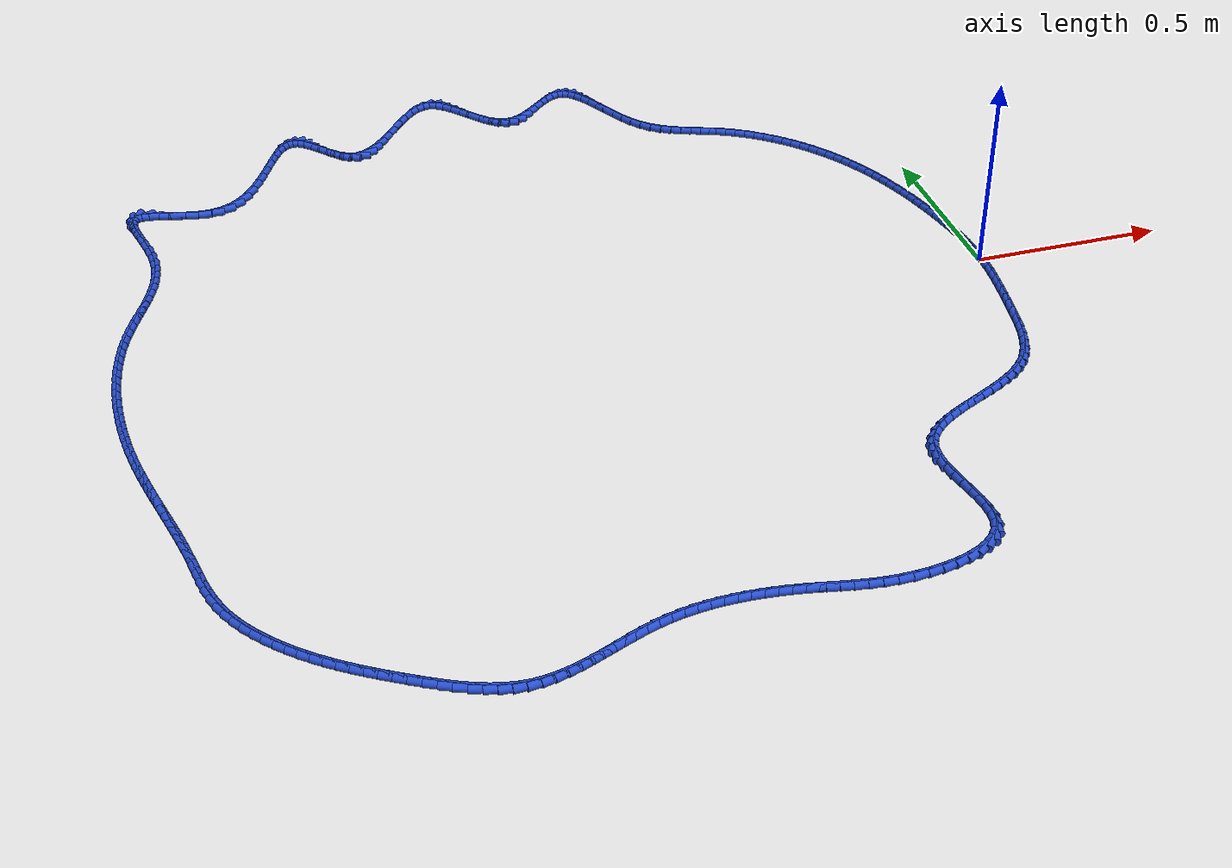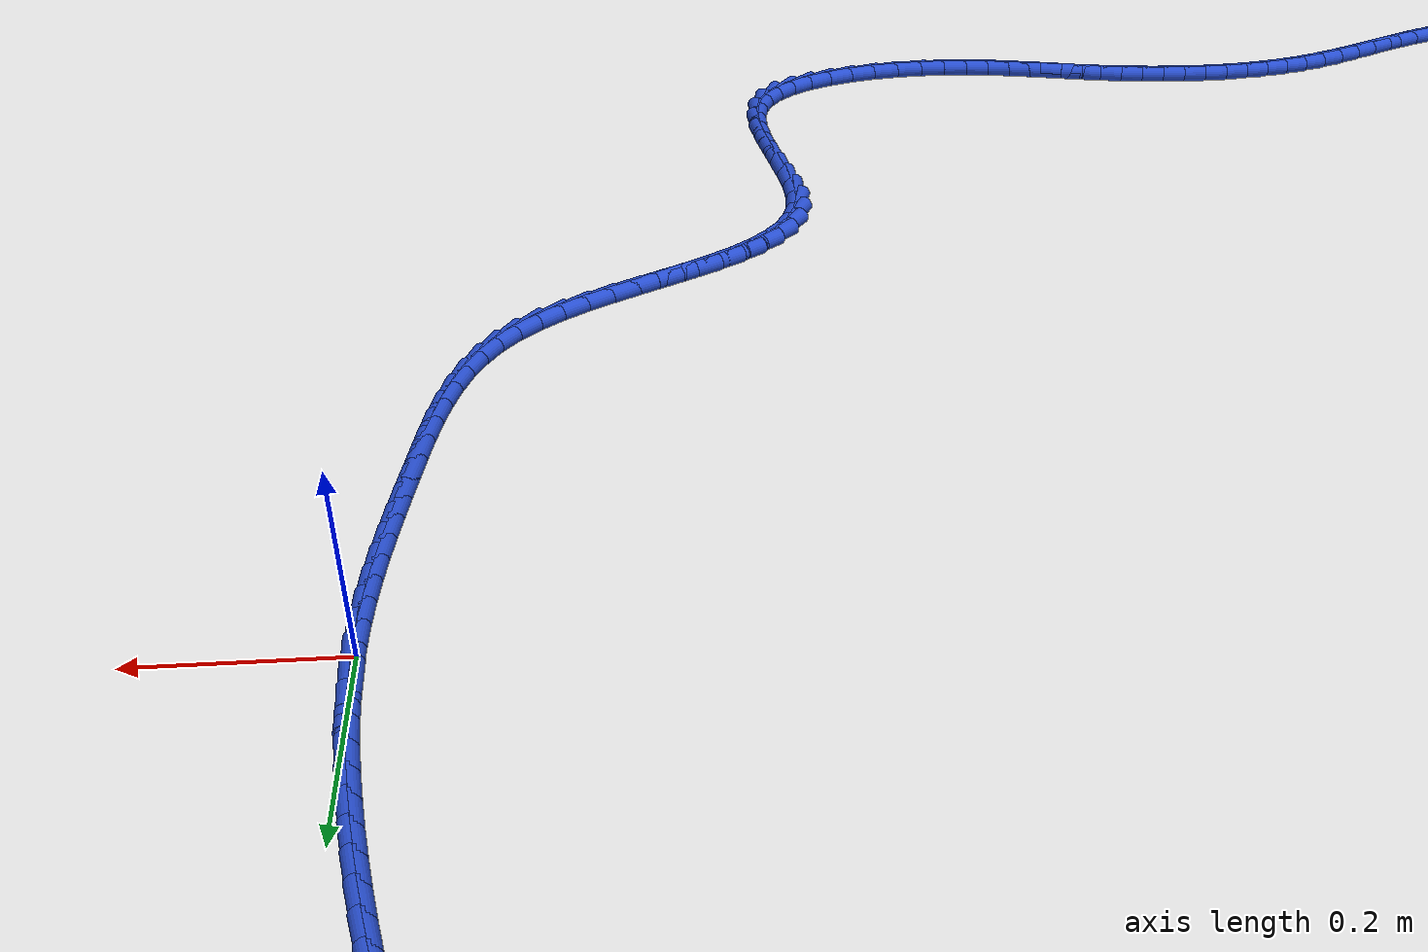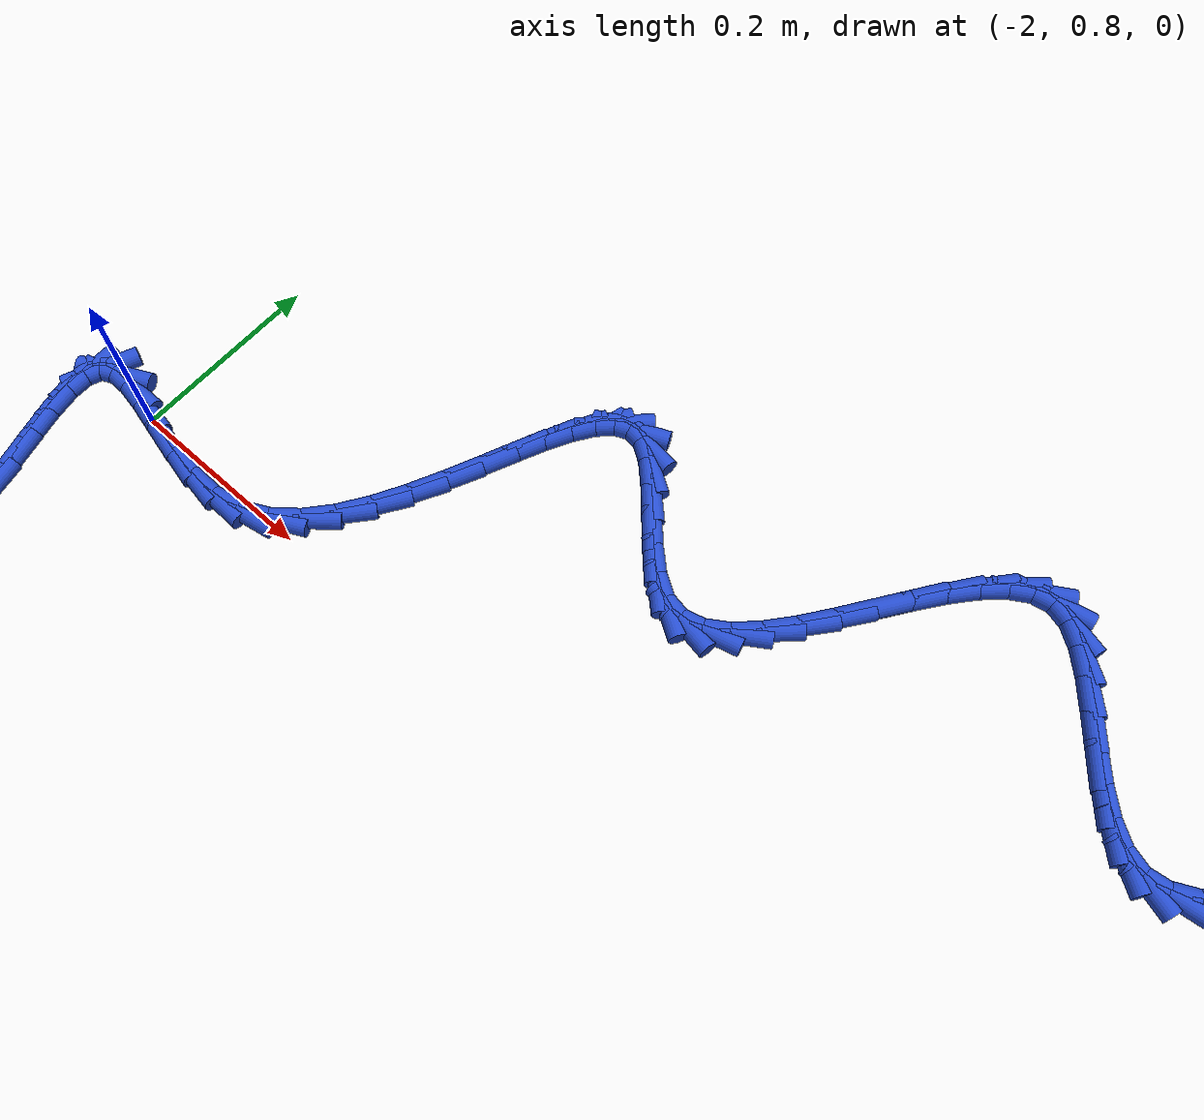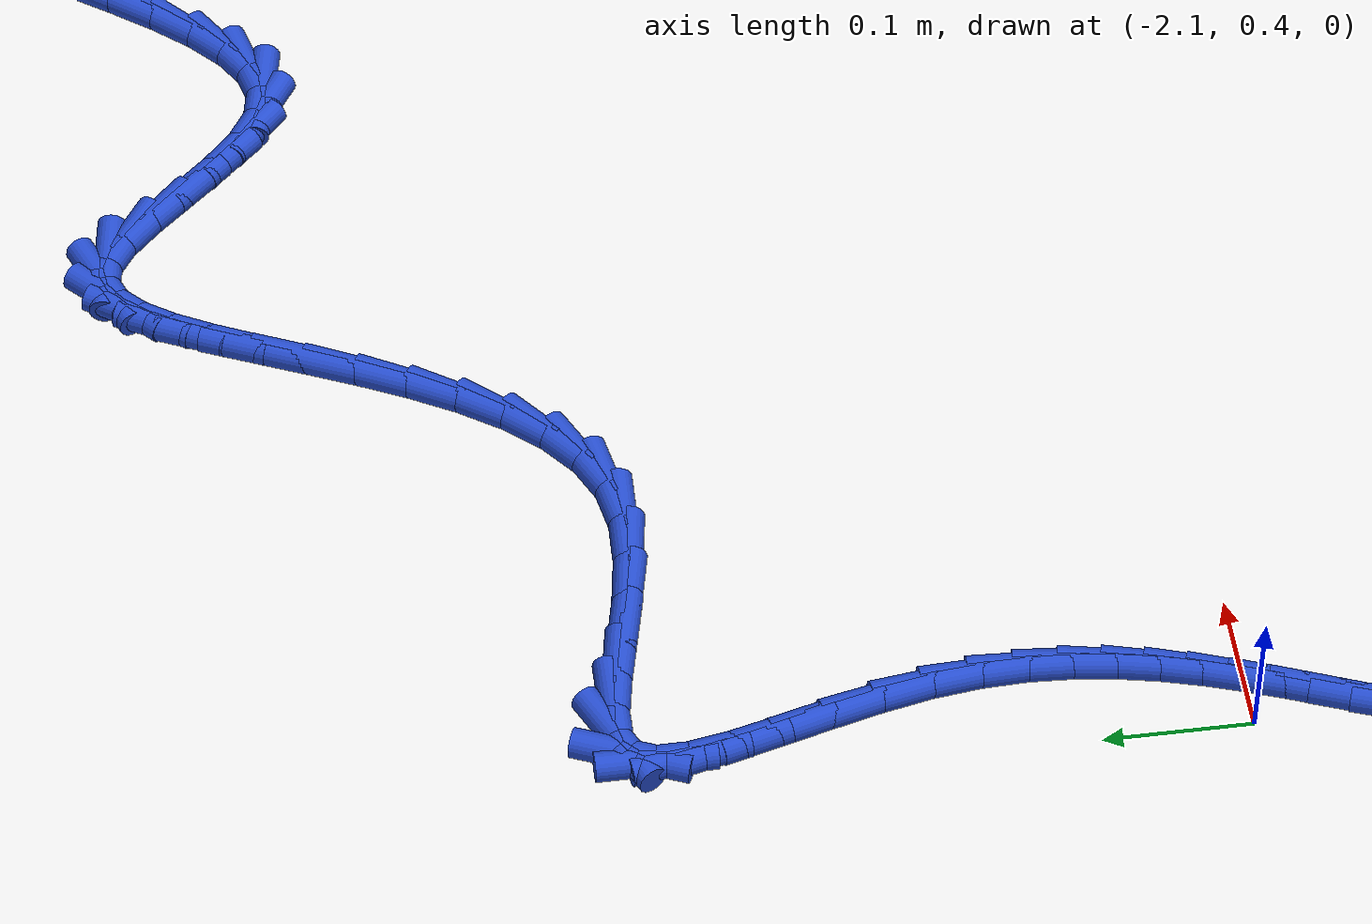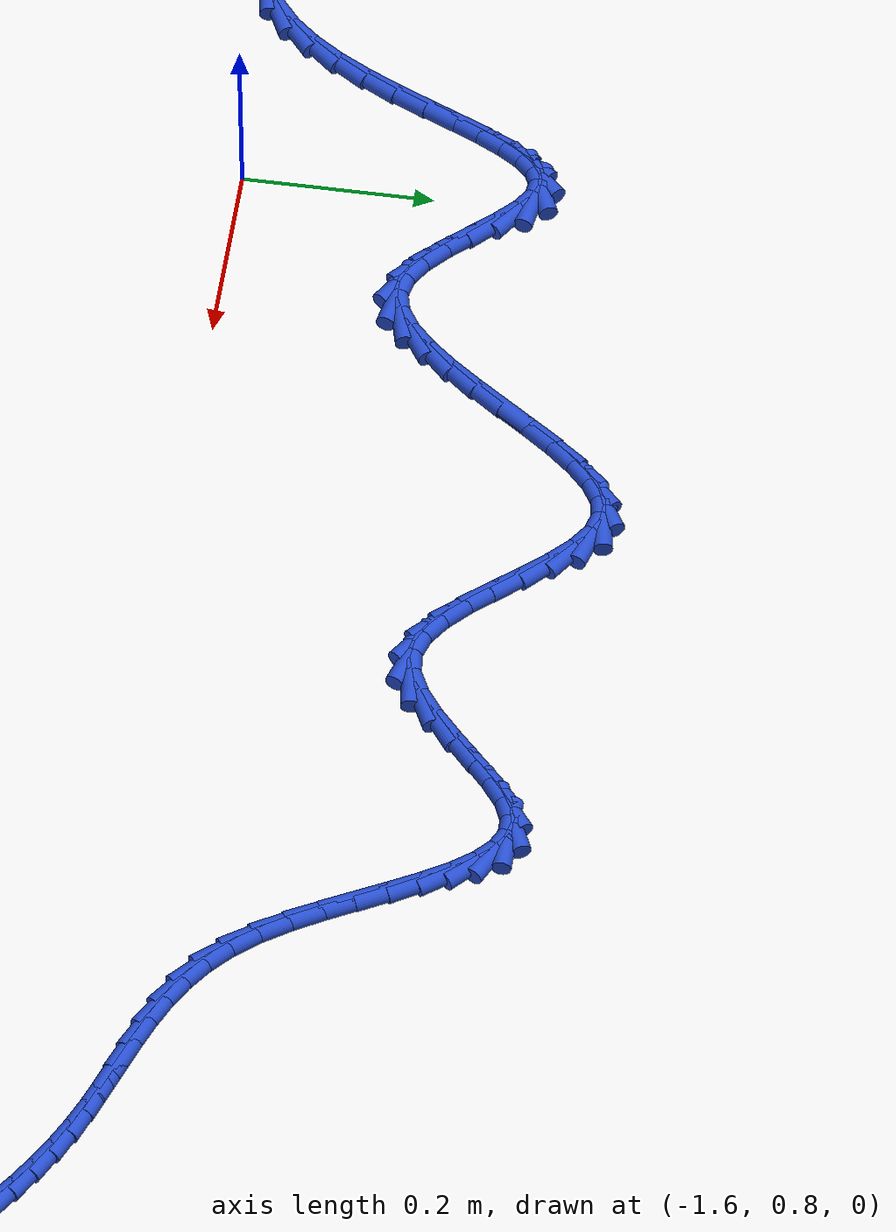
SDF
<sdf version="1.6">
 <world name="default">
  <light name="sun" type="directional">
   <pose>0 0 10 0 -0 0</pose>
   <diffuse>0.8 0.8 0.8 1</diffuse>
   <specular>0.2 0.2 0.2 1</specular>
   <attenuation>
    <range>1000</range>
    <constant>0.9</constant>
    <linear>0.01</linear>
    <quadratic>0.001</quadratic>
   </attenuation>
   <direction>-0.5 0.1 -0.9</direction>
  </light>
  <model name="ground_plane">
   <static>1</static>
   <link name="link">
    <collision name="collision">
     <geometry><plane><normal>0 0 1</normal><size>100 100</size></plane></geometry>
     <surface><friction><ode><mu>100</mu><mu2>50</mu2></ode></friction></surface>
    </collision>
    <visual name="visual">
     <cast_shadows>0</cast_shadows>
     <geometry><plane><normal>0 0 1</normal><size>100 100</size></plane></geometry>
     <material>
      <script><uri>file://media/materials/scripts/gazebo.material</uri><name>Gazebo/WhiteGlow</name></script>
     </material>
    </visual>
   </link>
  </model>
  <gravity>0 0 -9.8</gravity>
  <magnetic_field>6e-06 2.3e-05 -4.2e-05</magnetic_field>
  <atmosphere type="adiabatic"/>
  <physics name="default_physics" default="0" type="ode">
   <max_step_size>0.001</max_step_size>
   <real_time_factor>1</real_time_factor>
   <real_time_update_rate>1000</real_time_update_rate>
  </physics>
  <scene><ambient>0.4 0.4 0.4 1</ambient><background>0.7 0.7 0.7 1</background><shadows>1</shadows></scene>
  <spherical_coordinates>
   <surface_model>EARTH_WGS84</surface_model>
   <latitude_deg>0</latitude_deg>
   <longitude_deg>0</longitude_deg>
   <elevation>0</elevation>
   <heading_deg>0</heading_deg>
  </spherical_coordinates>
  <model name="line">
   <link name="link_0">
    <pose>-8.673617379884035e-18 -6.245004513516506e-17 0.01 0 1.57 -1.5623915560783812</pose>
    <collision name="collision">
     <geometry><cylinder><radius>0.01</radius><length>0.08</length></cylinder></geometry>
    </collision>
    <visual name="visual">
     <material>
      <script><name>Gazebo/Blue</name><uri>file://media/materials/scripts/gazebo.material</uri></script>
     </material>
     <geometry><cylinder><radius>0.01</radius><length>0.08</length></cylinder></geometry>
    </visual>
   </link>
   <link name="link_1">
    <pose>-0.00023429637923889668 0.027875937393561537 0.01 0 1.57 -1.5269187071183319</pose>
    <collision name="collision">
     <geometry><cylinder><radius>0.01</radius><length>0.08</length></cylinder></geometry>
    </collision>
    <visual name="visual">
     <material>
      <script><name>Gazebo/Blue</name><uri>file://media/materials/scripts/gazebo.material</uri></script>
     </material>
     <geometry><cylinder><radius>0.01</radius><length>0.08</length></cylinder></geometry>
    </visual>
   </link>
   <link name="link_2">
    <pose>-0.0014614901081974074 0.05582654381114246 0.01 0 1.57 -1.4943165975662682</pose>
    <collision name="collision">
     <geometry><cylinder><radius>0.01</radius><length>0.08</length></cylinder></geometry>
    </collision>
    <visual name="visual">
     <material>
      <script><name>Gazebo/Blue</name><uri>file://media/materials/scripts/gazebo.material</uri></script>
     </material>
     <geometry><cylinder><radius>0.01</radius><length>0.08</length></cylinder></geometry>
    </visual>
   </link>
   <link name="link_3">
    <pose>-0.003607352523385755 0.08382974127847832 0.01 0 1.57 -1.4645300538066999</pose>
    <collision name="collision">
     <geometry><cylinder><radius>0.01</radius><length>0.08</length></cylinder></geometry>
    </collision>
    <visual name="visual">
     <material>
      <script><name>Gazebo/Blue</name><uri>file://media/materials/scripts/gazebo.material</uri></script>
     </material>
     <geometry><cylinder><radius>0.01</radius><length>0.08</length></cylinder></geometry>
    </visual>
   </link>
   <link name="link_4">
    <pose>-0.0065976549613141495 0.1118634518213048 0.01 0 1.57 -1.437489420957152</pose>
    <collision name="collision">
     <geometry><cylinder><radius>0.01</radius><length>0.08</length></cylinder></geometry>
    </collision>
    <visual name="visual">
     <material>
      <script><name>Gazebo/Blue</name><uri>file://media/materials/scripts/gazebo.material</uri></script>
     </material>
     <geometry><cylinder><radius>0.01</radius><length>0.08</length></cylinder></geometry>
    </visual>
   </link>
   <link name="link_5">
    <pose>-0.010358168758492799 0.1399055974653575 0.01 0 1.57 -1.4131174889527256</pose>
    <collision name="collision">
     <geometry><cylinder><radius>0.01</radius><length>0.08</length></cylinder></geometry>
    </collision>
    <visual name="visual">
     <material>
      <script><name>Gazebo/Blue</name><uri>file://media/materials/scripts/gazebo.material</uri></script>
     </material>
     <geometry><cylinder><radius>0.01</radius><length>0.08</length></cylinder></geometry>
    </visual>
   </link>
   <link name="link_6">
    <pose>-0.014814665251431929 0.1679341002363722 0.01 0 1.57 -1.39133521005308</pose>
    <collision name="collision">
     <geometry><cylinder><radius>0.01</radius><length>0.08</length></cylinder></geometry>
    </collision>
    <visual name="visual">
     <material>
      <script><name>Gazebo/Blue</name><uri>file://media/materials/scripts/gazebo.material</uri></script>
     </material>
     <geometry><cylinder><radius>0.01</radius><length>0.08</length></cylinder></geometry>
    </visual>
   </link>
   <link name="link_7">
    <pose>-0.019892915776641748 0.19592688216008453 0.01 0 1.57 -1.372066318699521</pose>
    <collision name="collision">
     <geometry><cylinder><radius>0.01</radius><length>0.08</length></cylinder></geometry>
    </collision>
    <visual name="visual">
     <material>
      <script><name>Gazebo/Blue</name><uri>file://media/materials/scripts/gazebo.material</uri></script>
     </material>
     <geometry><cylinder><radius>0.01</radius><length>0.08</length></cylinder></geometry>
    </visual>
   </link>
   <link name="link_8">
    <pose>-0.025518691670632452 0.22386186526223 0.01 0 1.57 -1.3549656669186012</pose>
    <collision name="collision">
     <geometry><cylinder><radius>0.01</radius><length>0.08</length></cylinder></geometry>
    </collision>
    <visual name="visual">
     <material>
      <script><name>Gazebo/Blue</name><uri>file://media/materials/scripts/gazebo.material</uri></script>
     </material>
     <geometry><cylinder><radius>0.01</radius><length>0.08</length></cylinder></geometry>
    </visual>
   </link>
   <link name="link_9">
    <pose>-0.03162565596827973 0.2517163037976803 0.01 0 1.57 -1.3376442971754925</pose>
    <collision name="collision">
     <geometry><cylinder><radius>0.01</radius><length>0.08</length></cylinder></geometry>
    </collision>
    <visual name="visual">
     <material>
      <script><name>Gazebo/Blue</name><uri>file://media/materials/scripts/gazebo.material</uri></script>
     </material>
     <geometry><cylinder><radius>0.01</radius><length>0.08</length></cylinder></geometry>
    </visual>
   </link>
   <link name="link_10">
    <pose>-0.038214394773935435 0.2794617892002172 0.01 0 1.57 -1.3188914202939175</pose>
    <collision name="collision">
     <geometry><cylinder><radius>0.01</radius><length>0.08</length></cylinder></geometry>
    </collision>
    <visual name="visual">
     <material>
      <script><name>Gazebo/Blue</name><uri>file://media/materials/scripts/gazebo.material</uri></script>
     </material>
     <geometry><cylinder><radius>0.01</radius><length>0.08</length></cylinder></geometry>
    </visual>
   </link>
   <link name="link_11">
    <pose>-0.045319218790244274 0.3070670592334612 0.01 0 1.57 -1.2986659421992113</pose>
    <collision name="collision">
     <geometry><cylinder><radius>0.01</radius><length>0.08</length></cylinder></geometry>
    </collision>
    <visual name="visual">
     <material>
      <script><name>Gazebo/Blue</name><uri>file://media/materials/scripts/gazebo.material</uri></script>
     </material>
     <geometry><cylinder><radius>0.01</radius><length>0.08</length></cylinder></geometry>
    </visual>
   </link>
   <link name="link_12">
    <pose>-0.05297469626796127 0.3345008298681169 0.01 0 1.57 -1.2769356533541465</pose>
    <collision name="collision">
     <geometry><cylinder><radius>0.01</radius><length>0.08</length></cylinder></geometry>
    </collision>
    <visual name="visual">
     <material>
      <script><name>Gazebo/Blue</name><uri>file://media/materials/scripts/gazebo.material</uri></script>
     </material>
     <geometry><cylinder><radius>0.01</radius><length>0.08</length></cylinder></geometry>
    </visual>
   </link>
   <link name="link_13">
    <pose>-0.061215395457841486 0.36173181707488805 0.01 0 1.57 -1.2536695181772743</pose>
    <collision name="collision">
     <geometry><cylinder><radius>0.01</radius><length>0.08</length></cylinder></geometry>
    </collision>
    <visual name="visual">
     <material>
      <script><name>Gazebo/Blue</name><uri>file://media/materials/scripts/gazebo.material</uri></script>
     </material>
     <geometry><cylinder><radius>0.01</radius><length>0.08</length></cylinder></geometry>
    </visual>
   </link>
   <link name="link_14">
    <pose>-0.07007588461063995 0.38872873682447906 0.01 0 1.57 -1.228839149628577</pose>
    <collision name="collision">
     <geometry><cylinder><radius>0.01</radius><length>0.08</length></cylinder></geometry>
    </collision>
    <visual name="visual">
     <material>
      <script><name>Gazebo/Blue</name><uri>file://media/materials/scripts/gazebo.material</uri></script>
     </material>
     <geometry><cylinder><radius>0.01</radius><length>0.08</length></cylinder></geometry>
    </visual>
   </link>
   <link name="link_15">
    <pose>-0.0795907319771117 0.41546030508759385 0.01 0 1.57 -1.2024204957721947</pose>
    <collision name="collision">
     <geometry><cylinder><radius>0.01</radius><length>0.08</length></cylinder></geometry>
    </collision>
    <visual name="visual">
     <material>
      <script><name>Gazebo/Blue</name><uri>file://media/materials/scripts/gazebo.material</uri></script>
     </material>
     <geometry><cylinder><radius>0.01</radius><length>0.08</length></cylinder></geometry>
    </visual>
   </link>
   <link name="link_16">
    <pose>-0.08979450580801174 0.4418952378349365 0.01 0 1.57 -1.1743957397551579</pose>
    <collision name="collision">
     <geometry><cylinder><radius>0.01</radius><length>0.08</length></cylinder></geometry>
    </collision>
    <visual name="visual">
     <material>
      <script><name>Gazebo/Blue</name><uri>file://media/materials/scripts/gazebo.material</uri></script>
     </material>
     <geometry><cylinder><radius>0.01</radius><length>0.08</length></cylinder></geometry>
    </visual>
   </link>
   <link name="link_17">
    <pose>-0.10072177435409517 0.46800225103721155 0.01 0 1.57 -1.1447553988098094</pose>
    <collision name="collision">
     <geometry><cylinder><radius>0.01</radius><length>0.08</length></cylinder></geometry>
    </collision>
    <visual name="visual">
     <material>
      <script><name>Gazebo/Blue</name><uri>file://media/materials/scripts/gazebo.material</uri></script>
     </material>
     <geometry><cylinder><radius>0.01</radius><length>0.08</length></cylinder></geometry>
    </visual>
   </link>
   <link name="link_18">
    <pose>-0.11240710586611694 0.4937500606651226 0.01 0 1.57 -1.1135005869287327</pose>
    <collision name="collision">
     <geometry><cylinder><radius>0.01</radius><length>0.08</length></cylinder></geometry>
    </collision>
    <visual name="visual">
     <material>
      <script><name>Gazebo/Blue</name><uri>file://media/materials/scripts/gazebo.material</uri></script>
     </material>
     <geometry><cylinder><radius>0.01</radius><length>0.08</length></cylinder></geometry>
    </visual>
   </link>
   <link name="link_19">
    <pose>-0.1248850685948322 0.5191073826893744 0.01 0 1.57 -1.0806453798587448</pose>
    <collision name="collision">
     <geometry><cylinder><radius>0.01</radius><length>0.08</length></cylinder></geometry>
    </collision>
    <visual name="visual">
     <material>
      <script><name>Gazebo/Blue</name><uri>file://media/materials/scripts/gazebo.material</uri></script>
     </material>
     <geometry><cylinder><radius>0.01</radius><length>0.08</length></cylinder></geometry>
    </visual>
   </link>
   <link name="link_20">
    <pose>-0.1381902307909959 0.5440429330806705 0.01 0 1.57 -1.0462191909756156</pose>
    <collision name="collision">
     <geometry><cylinder><radius>0.01</radius><length>0.08</length></cylinder></geometry>
    </collision>
    <visual name="visual">
     <material>
      <script><name>Gazebo/Blue</name><uri>file://media/materials/scripts/gazebo.material</uri></script>
     </material>
     <geometry><cylinder><radius>0.01</radius><length>0.08</length></cylinder></geometry>
    </visual>
   </link>
   <link name="link_21">
    <pose>-0.15235716070536312 0.5685254278097154 0.01 0 1.57 -1.0102690345931147</pose>
    <collision name="collision">
     <geometry><cylinder><radius>0.01</radius><length>0.08</length></cylinder></geometry>
    </collision>
    <visual name="visual">
     <material>
      <script><name>Gazebo/Blue</name><uri>file://media/materials/scripts/gazebo.material</uri></script>
     </material>
     <geometry><cylinder><radius>0.01</radius><length>0.08</length></cylinder></geometry>
    </visual>
   </link>
   <link name="link_22">
    <pose>-0.16742042658868891 0.5925235828472133 0.01 0 1.57 -0.9728615229176963</pose>
    <collision name="collision">
     <geometry><cylinder><radius>0.01</radius><length>0.08</length></cylinder></geometry>
    </collision>
    <visual name="visual">
     <material>
      <script><name>Gazebo/Blue</name><uri>file://media/materials/scripts/gazebo.material</uri></script>
     </material>
     <geometry><cylinder><radius>0.01</radius><length>0.08</length></cylinder></geometry>
    </visual>
   </link>
   <link name="link_23">
    <pose>-0.18341459669172822 0.6160061141638681 0.01 0 1.57 -0.934108247288026</pose>
    <collision name="collision">
     <geometry><cylinder><radius>0.01</radius><length>0.08</length></cylinder></geometry>
    </collision>
    <visual name="visual">
     <material>
      <script><name>Gazebo/Blue</name><uri>file://media/materials/scripts/gazebo.material</uri></script>
     </material>
     <geometry><cylinder><radius>0.01</radius><length>0.08</length></cylinder></geometry>
    </visual>
   </link>
   <link name="link_24">
    <pose>-0.20037212419622707 0.6389400204796291 0.01 0 1.57 -0.8944481296883096</pose>
    <collision name="collision">
     <geometry><cylinder><radius>0.01</radius><length>0.08</length></cylinder></geometry>
    </collision>
    <visual name="visual">
     <material>
      <script><name>Gazebo/Blue</name><uri>file://media/materials/scripts/gazebo.material</uri></script>
     </material>
     <geometry><cylinder><radius>0.01</radius><length>0.08</length></cylinder></geometry>
    </visual>
   </link>
   <link name="link_25">
    <pose>-0.2182895195742106 0.661263118182745 0.01 0 1.57 -0.8540329866886747</pose>
    <collision name="collision">
     <geometry><cylinder><radius>0.01</radius><length>0.08</length></cylinder></geometry>
    </collision>
    <visual name="visual">
     <material>
      <script><name>Gazebo/Blue</name><uri>file://media/materials/scripts/gazebo.material</uri></script>
     </material>
     <geometry><cylinder><radius>0.01</radius><length>0.08</length></cylinder></geometry>
    </visual>
   </link>
   <link name="link_26">
    <pose>-0.2371332489161435 0.6828888302555329 0.01 0 1.57 -0.8126335712561945</pose>
    <collision name="collision">
     <geometry><cylinder><radius>0.01</radius><length>0.08</length></cylinder></geometry>
    </collision>
    <visual name="visual">
     <material>
      <script><name>Gazebo/Blue</name><uri>file://media/materials/scripts/gazebo.material</uri></script>
     </material>
     <geometry><cylinder><radius>0.01</radius><length>0.08</length></cylinder></geometry>
    </visual>
   </link>
   <link name="link_27">
    <pose>-0.2568688548037551 0.7037298298721174 0.01 0 1.57 -0.7700139202231988</pose>
    <collision name="collision">
     <geometry><cylinder><radius>0.01</radius><length>0.08</length></cylinder></geometry>
    </collision>
    <visual name="visual">
     <material>
      <script><name>Gazebo/Blue</name><uri>file://media/materials/scripts/gazebo.material</uri></script>
     </material>
     <geometry><cylinder><radius>0.01</radius><length>0.08</length></cylinder></geometry>
    </visual>
   </link>
   <link name="link_28">
    <pose>-0.2774618798187741 0.7236987902066223 0.01 0 1.57 -0.725941843986509</pose>
    <collision name="collision">
     <geometry><cylinder><radius>0.01</radius><length>0.08</length></cylinder></geometry>
    </collision>
    <visual name="visual">
     <material>
      <script><name>Gazebo/Blue</name><uri>file://media/materials/scripts/gazebo.material</uri></script>
     </material>
     <geometry><cylinder><radius>0.01</radius><length>0.08</length></cylinder></geometry>
    </visual>
   </link>
   <link name="link_29">
    <pose>-0.2988778665429295 0.7427083844331717 0.01 0 1.57 -0.6801902253976636</pose>
    <collision name="collision">
     <geometry><cylinder><radius>0.01</radius><length>0.08</length></cylinder></geometry>
    </collision>
    <visual name="visual">
     <material>
      <script><name>Gazebo/Blue</name><uri>file://media/materials/scripts/gazebo.material</uri></script>
     </material>
     <geometry><cylinder><radius>0.01</radius><length>0.08</length></cylinder></geometry>
    </visual>
   </link>
   <link name="link_30">
    <pose>-0.32108235755795034 0.7606712857258892 0.01 0 1.57 -0.6325397799458747</pose>
    <collision name="collision">
     <geometry><cylinder><radius>0.01</radius><length>0.08</length></cylinder></geometry>
    </collision>
    <visual name="visual">
     <material>
      <script><name>Gazebo/Blue</name><uri>file://media/materials/scripts/gazebo.material</uri></script>
     </material>
     <geometry><cylinder><radius>0.01</radius><length>0.08</length></cylinder></geometry>
    </visual>
   </link>
   <link name="link_31">
    <pose>-0.3440408954455655 0.7775001672588991 0.01 0 1.57 -0.5827835536035806</pose>
    <collision name="collision">
     <geometry><cylinder><radius>0.01</radius><length>0.08</length></cylinder></geometry>
    </collision>
    <visual name="visual">
     <material>
      <script><name>Gazebo/Blue</name><uri>file://media/materials/scripts/gazebo.material</uri></script>
     </material>
     <geometry><cylinder><radius>0.01</radius><length>0.08</length></cylinder></geometry>
    </visual>
   </link>
   <link name="link_32">
    <pose>-0.36771902278750407 0.7931077022063253 0.01 0 1.57 -0.5307334299179657</pose>
    <collision name="collision">
     <geometry><cylinder><radius>0.01</radius><length>0.08</length></cylinder></geometry>
    </collision>
    <visual name="visual">
     <material>
      <script><name>Gazebo/Blue</name><uri>file://media/materials/scripts/gazebo.material</uri></script>
     </material>
     <geometry><cylinder><radius>0.01</radius><length>0.08</length></cylinder></geometry>
    </visual>
   </link>
   <link name="link_33">
    <pose>-0.3920822821654948 0.8074065637422917 0.01 0 1.57 -0.4762288524280387</pose>
    <collision name="collision">
     <geometry><cylinder><radius>0.01</radius><length>0.08</length></cylinder></geometry>
    </collision>
    <visual name="visual">
     <material>
      <script><name>Gazebo/Blue</name><uri>file://media/materials/scripts/gazebo.material</uri></script>
     </material>
     <geometry><cylinder><radius>0.01</radius><length>0.08</length></cylinder></geometry>
    </visual>
   </link>
   <link name="link_34">
    <pose>-0.41709621616126674 0.8203094250409222 0.01 0 1.57 -0.41938294566894946</pose>
    <collision name="collision">
     <geometry><cylinder><radius>0.01</radius><length>0.08</length></cylinder></geometry>
    </collision>
    <visual name="visual">
     <material>
      <script><name>Gazebo/Blue</name><uri>file://media/materials/scripts/gazebo.material</uri></script>
     </material>
     <geometry><cylinder><radius>0.01</radius><length>0.08</length></cylinder></geometry>
    </visual>
   </link>
   <link name="link_35">
    <pose>-0.44272442109272364 0.8317353152637407 0.01 0 1.57 -0.3715520825842486</pose>
    <collision name="collision">
     <geometry><cylinder><radius>0.01</radius><length>0.08</length></cylinder></geometry>
    </collision>
    <visual name="visual">
     <material>
      <script><name>Gazebo/Blue</name><uri>file://media/materials/scripts/gazebo.material</uri></script>
     </material>
     <geometry><cylinder><radius>0.01</radius><length>0.08</length></cylinder></geometry>
    </visual>
   </link>
   <link name="link_36">
    <pose>-0.4688365927517917 0.8419099180721734 0.01 0 1.57 -0.34911978540265187</pose>
    <collision name="collision">
     <geometry><cylinder><radius>0.01</radius><length>0.08</length></cylinder></geometry>
    </collision>
    <visual name="visual">
     <material>
      <script><name>Gazebo/Blue</name><uri>file://media/materials/scripts/gazebo.material</uri></script>
     </material>
     <geometry><cylinder><radius>0.01</radius><length>0.08</length></cylinder></geometry>
    </visual>
   </link>
   <link name="link_37">
    <pose>-0.4951687012425502 0.8514956301652337 0.01 0 1.57 -0.35336956734753167</pose>
    <collision name="collision">
     <geometry><cylinder><radius>0.01</radius><length>0.08</length></cylinder></geometry>
    </collision>
    <visual name="visual">
     <material>
      <script><name>Gazebo/Blue</name><uri>file://media/materials/scripts/gazebo.material</uri></script>
     </material>
     <geometry><cylinder><radius>0.01</radius><length>0.08</length></cylinder></geometry>
    </visual>
   </link>
   <link name="link_38">
    <pose>-0.5214464919443004 0.861188239512437 0.01 0 1.57 -0.3843411002504752</pose>
    <collision name="collision">
     <geometry><cylinder><radius>0.01</radius><length>0.08</length></cylinder></geometry>
    </collision>
    <visual name="visual">
     <material>
      <script><name>Gazebo/Blue</name><uri>file://media/materials/scripts/gazebo.material</uri></script>
     </material>
     <geometry><cylinder><radius>0.01</radius><length>0.08</length></cylinder></geometry>
    </visual>
   </link>
   <link name="link_39">
    <pose>-0.547395710236344 0.8716835340833003 0.01 0 1.57 -0.44197401316748347</pose>
    <collision name="collision">
     <geometry><cylinder><radius>0.01</radius><length>0.08</length></cylinder></geometry>
    </collision>
    <visual name="visual">
     <material>
      <script><name>Gazebo/Blue</name><uri>file://media/materials/scripts/gazebo.material</uri></script>
     </material>
     <geometry><cylinder><radius>0.01</radius><length>0.08</length></cylinder></geometry>
    </visual>
   </link>
   <link name="link_40">
    <pose>-0.5727421014979822 0.8836773018473388 0.01 0 1.57 -0.5254562444469503</pose>
    <collision name="collision">
     <geometry><cylinder><radius>0.01</radius><length>0.08</length></cylinder></geometry>
    </collision>
    <visual name="visual">
     <material>
      <script><name>Gazebo/Blue</name><uri>file://media/materials/scripts/gazebo.material</uri></script>
     </material>
     <geometry><cylinder><radius>0.01</radius><length>0.08</length></cylinder></geometry>
    </visual>
   </link>
   <link name="link_41">
    <pose>-0.5972114111085175 0.89786533077407 0.01 0 1.57 -0.6321414716892398</pose>
    <collision name="collision">
     <geometry><cylinder><radius>0.01</radius><length>0.08</length></cylinder></geometry>
    </collision>
    <visual name="visual">
     <material>
      <script><name>Gazebo/Blue</name><uri>file://media/materials/scripts/gazebo.material</uri></script>
     </material>
     <geometry><cylinder><radius>0.01</radius><length>0.08</length></cylinder></geometry>
    </visual>
   </link>
   <link name="link_42">
    <pose>-0.6205293844472503 0.9149434088330088 0.01 0 1.57 -0.7565393035027346</pose>
    <collision name="collision">
     <geometry><cylinder><radius>0.01</radius><length>0.08</length></cylinder></geometry>
    </collision>
    <visual name="visual">
     <material>
      <script><name>Gazebo/Blue</name><uri>file://media/materials/scripts/gazebo.material</uri></script>
     </material>
     <geometry><cylinder><radius>0.01</radius><length>0.08</length></cylinder></geometry>
    </visual>
   </link>
   <link name="link_43">
    <pose>-0.6424217668934827 0.9356073239936726 0.01 0 1.57 -0.887298377264902</pose>
    <collision name="collision">
     <geometry><cylinder><radius>0.01</radius><length>0.08</length></cylinder></geometry>
    </collision>
    <visual name="visual">
     <material>
      <script><name>Gazebo/Blue</name><uri>file://media/materials/scripts/gazebo.material</uri></script>
     </material>
     <geometry><cylinder><radius>0.01</radius><length>0.08</length></cylinder></geometry>
    </visual>
   </link>
   <link name="link_44">
    <pose>-0.6626471352729101 0.9604400834730122 0.01 0 1.57 -0.9892418732384034</pose>
    <collision name="collision">
     <geometry><cylinder><radius>0.01</radius><length>0.08</length></cylinder></geometry>
    </collision>
    <visual name="visual">
     <material>
      <script><name>Gazebo/Blue</name><uri>file://media/materials/scripts/gazebo.material</uri></script>
     </material>
     <geometry><cylinder><radius>0.01</radius><length>0.08</length></cylinder></geometry>
    </visual>
   </link>
   <link name="link_45">
    <pose>-0.6813114221710953 0.9888314773651247 0.01 0 1.57 -1.05363710817512</pose>
    <collision name="collision">
     <geometry><cylinder><radius>0.01</radius><length>0.08</length></cylinder></geometry>
    </collision>
    <visual name="visual">
     <material>
      <script><name>Gazebo/Blue</name><uri>file://media/materials/scripts/gazebo.material</uri></script>
     </material>
     <geometry><cylinder><radius>0.01</radius><length>0.08</length></cylinder></geometry>
    </visual>
   </link>
   <link name="link_46">
    <pose>-0.6987293764573156 1.0194539817188295 0.01 0 1.57 -1.0887638676970899</pose>
    <collision name="collision">
     <geometry><cylinder><radius>0.01</radius><length>0.08</length></cylinder></geometry>
    </collision>
    <visual name="visual">
     <material>
      <script><name>Gazebo/Blue</name><uri>file://media/materials/scripts/gazebo.material</uri></script>
     </material>
     <geometry><cylinder><radius>0.01</radius><length>0.08</length></cylinder></geometry>
    </visual>
   </link>
   <link name="link_47">
    <pose>-0.7152186008135264 1.050970269324891 0.01 0 1.57 -1.0983894036347013</pose>
    <collision name="collision">
     <geometry><cylinder><radius>0.01</radius><length>0.08</length></cylinder></geometry>
    </collision>
    <visual name="visual">
     <material>
      <script><name>Gazebo/Blue</name><uri>file://media/materials/scripts/gazebo.material</uri></script>
     </material>
     <geometry><cylinder><radius>0.01</radius><length>0.08</length></cylinder></geometry>
    </visual>
   </link>
   <link name="link_48">
    <pose>-0.7310966979216817 1.0820430129740726 0.01 0 1.57 -1.0818431435363232</pose>
    <collision name="collision">
     <geometry><cylinder><radius>0.01</radius><length>0.08</length></cylinder></geometry>
    </collision>
    <visual name="visual">
     <material>
      <script><name>Gazebo/Blue</name><uri>file://media/materials/scripts/gazebo.material</uri></script>
     </material>
     <geometry><cylinder><radius>0.01</radius><length>0.08</length></cylinder></geometry>
    </visual>
   </link>
   <link name="link_49">
    <pose>-0.7466812704637367 1.1113348854571383 0.01 0 1.57 -1.0330655330375513</pose>
    <collision name="collision">
     <geometry><cylinder><radius>0.01</radius><length>0.08</length></cylinder></geometry>
    </collision>
    <visual name="visual">
     <material>
      <script><name>Gazebo/Blue</name><uri>file://media/materials/scripts/gazebo.material</uri></script>
     </material>
     <geometry><cylinder><radius>0.01</radius><length>0.08</length></cylinder></geometry>
    </visual>
   </link>
   <link name="link_50">
    <pose>-0.7622899211216458 1.1375085595648509 0.01 0 1.57 -0.9373385538858532</pose>
    <collision name="collision">
     <geometry><cylinder><radius>0.01</radius><length>0.08</length></cylinder></geometry>
    </collision>
    <visual name="visual">
     <material>
      <script><name>Gazebo/Blue</name><uri>file://media/materials/scripts/gazebo.material</uri></script>
     </material>
     <geometry><cylinder><radius>0.01</radius><length>0.08</length></cylinder></geometry>
    </visual>
   </link>
   <link name="link_51">
    <pose>-0.778240252577364 1.1592267080879748 0.01 0 1.57 -0.7643678822628867</pose>
    <collision name="collision">
     <geometry><cylinder><radius>0.01</radius><length>0.08</length></cylinder></geometry>
    </collision>
    <visual name="visual">
     <material>
      <script><name>Gazebo/Blue</name><uri>file://media/materials/scripts/gazebo.material</uri></script>
     </material>
     <geometry><cylinder><radius>0.01</radius><length>0.08</length></cylinder></geometry>
    </visual>
   </link>
   <link name="link_52">
    <pose>-0.7948498675128458 1.1751520038172738 0.01 0 1.57 -0.46373245127838336</pose>
    <collision name="collision">
     <geometry><cylinder><radius>0.01</radius><length>0.08</length></cylinder></geometry>
    </collision>
    <visual name="visual">
     <material>
      <script><name>Gazebo/Blue</name><uri>file://media/materials/scripts/gazebo.material</uri></script>
     </material>
     <geometry><cylinder><radius>0.01</radius><length>0.08</length></cylinder></geometry>
    </visual>
   </link>
   <link name="link_53">
    <pose>-0.812436368610046 1.183947119543511 0.01 0 1.57 -0.017349495111616535</pose>
    <collision name="collision">
     <geometry><cylinder><radius>0.01</radius><length>0.08</length></cylinder></geometry>
    </collision>
    <visual name="visual">
     <material>
      <script><name>Gazebo/Blue</name><uri>file://media/materials/scripts/gazebo.material</uri></script>
     </material>
     <geometry><cylinder><radius>0.01</radius><length>0.08</length></cylinder></geometry>
    </visual>
   </link>
   <link name="link_54">
    <pose>-0.8313173585509193 1.1842747280574504 0.01 0 1.57 0.4126202887257371</pose>
    <collision name="collision">
     <geometry><cylinder><radius>0.01</radius><length>0.08</length></cylinder></geometry>
    </collision>
    <visual name="visual">
     <material>
      <script><name>Gazebo/Blue</name><uri>file://media/materials/scripts/gazebo.material</uri></script>
     </material>
     <geometry><cylinder><radius>0.01</radius><length>0.08</length></cylinder></geometry>
    </visual>
   </link>
   <link name="link_55">
    <pose>-0.8517294286098305 1.1753393436514845 0.01 0 1.57 0.6422386287900617</pose>
    <collision name="collision">
     <geometry><cylinder><radius>0.01</radius><length>0.08</length></cylinder></geometry>
    </collision>
    <visual name="visual">
     <material>
      <script><name>Gazebo/Blue</name><uri>file://media/materials/scripts/gazebo.material</uri></script>
     </material>
     <geometry><cylinder><radius>0.01</radius><length>0.08</length></cylinder></geometry>
    </visual>
   </link>
   <link name="link_56">
    <pose>-0.873504692965595 1.15905080920504 0.01 0 1.57 0.7407171454707382</pose>
    <collision name="collision">
     <geometry><cylinder><radius>0.01</radius><length>0.08</length></cylinder></geometry>
    </collision>
    <visual name="visual">
     <material>
      <script><name>Gazebo/Blue</name><uri>file://media/materials/scripts/gazebo.material</uri></script>
     </material>
     <geometry><cylinder><radius>0.01</radius><length>0.08</length></cylinder></geometry>
    </visual>
   </link>
   <link name="link_57">
    <pose>-0.896349284175867 1.1381615905418692 0.01 0 1.57 0.766356047504057</pose>
    <collision name="collision">
     <geometry><cylinder><radius>0.01</radius><length>0.08</length></cylinder></geometry>
    </collision>
    <visual name="visual">
     <material>
      <script><name>Gazebo/Blue</name><uri>file://media/materials/scripts/gazebo.material</uri></script>
     </material>
     <geometry><cylinder><radius>0.01</radius><length>0.08</length></cylinder></geometry>
    </visual>
   </link>
   <link name="link_58">
    <pose>-0.9199692940438952 1.1154244260699138 0.01 0 1.57 0.7360379812707823</pose>
    <collision name="collision">
     <geometry><cylinder><radius>0.01</radius><length>0.08</length></cylinder></geometry>
    </collision>
    <visual name="visual">
     <material>
      <script><name>Gazebo/Blue</name><uri>file://media/materials/scripts/gazebo.material</uri></script>
     </material>
     <geometry><cylinder><radius>0.01</radius><length>0.08</length></cylinder></geometry>
    </visual>
   </link>
   <link name="link_59">
    <pose>-0.9440708143729273 1.0935920541971154 0.01 0 1.57 0.6423934932449865</pose>
    <collision name="collision">
     <geometry><cylinder><radius>0.01</radius><length>0.08</length></cylinder></geometry>
    </collision>
    <visual name="visual">
     <material>
      <script><name>Gazebo/Blue</name><uri>file://media/materials/scripts/gazebo.material</uri></script>
     </material>
     <geometry><cylinder><radius>0.01</radius><length>0.08</length></cylinder></geometry>
    </visual>
   </link>
   <link name="link_60">
    <pose>-0.9683599369662113 1.075417213331415 0.01 0 1.57 0.45277706542278295</pose>
    <collision name="collision">
     <geometry><cylinder><radius>0.01</radius><length>0.08</length></cylinder></geometry>
    </collision>
    <visual name="visual">
     <material>
      <script><name>Gazebo/Blue</name><uri>file://media/materials/scripts/gazebo.material</uri></script>
     </material>
     <geometry><cylinder><radius>0.01</radius><length>0.08</length></cylinder></geometry>
    </visual>
   </link>
   <link name="link_61">
    <pose>-0.9925427536269956 1.0636526418807553 0.01 0 1.57 0.10952757377420752</pose>
    <collision name="collision">
     <geometry><cylinder><radius>0.01</radius><length>0.08</length></cylinder></geometry>
    </collision>
    <visual name="visual">
     <material>
      <script><name>Gazebo/Blue</name><uri>file://media/materials/scripts/gazebo.material</uri></script>
     </material>
     <geometry><cylinder><radius>0.01</radius><length>0.08</length></cylinder></geometry>
    </visual>
   </link>
   <link name="link_62">
    <pose>-1.0163263213612683 1.0610372185790873 0.01 0 1.57 -0.3180639549718898</pose>
    <collision name="collision">
     <geometry><cylinder><radius>0.01</radius><length>0.08</length></cylinder></geometry>
    </collision>
    <visual name="visual">
     <material>
      <script><name>Gazebo/Blue</name><uri>file://media/materials/scripts/gazebo.material</uri></script>
     </material>
     <geometry><cylinder><radius>0.01</radius><length>0.08</length></cylinder></geometry>
    </visual>
   </link>
   <link name="link_63">
    <pose>-1.0395313875272298 1.0686773037761683 0.01 0 1.57 -0.6103851089538807</pose>
    <collision name="collision">
     <geometry><cylinder><radius>0.01</radius><length>0.08</length></cylinder></geometry>
    </collision>
    <visual name="visual">
     <material>
      <script><name>Gazebo/Blue</name><uri>file://media/materials/scripts/gazebo.material</uri></script>
     </material>
     <geometry><cylinder><radius>0.01</radius><length>0.08</length></cylinder></geometry>
    </visual>
   </link>
   <link name="link_64">
    <pose>-1.062197855483766 1.0845323223680103 0.01 0 1.57 -0.7735066864701194</pose>
    <collision name="collision">
     <geometry><cylinder><radius>0.01</radius><length>0.08</length></cylinder></geometry>
    </collision>
    <visual name="visual">
     <material>
      <script><name>Gazebo/Blue</name><uri>file://media/materials/scripts/gazebo.material</uri></script>
     </material>
     <geometry><cylinder><radius>0.01</radius><length>0.08</length></cylinder></geometry>
    </visual>
   </link>
   <link name="link_65">
    <pose>-1.0843905797893263 1.1062034165010073 0.01 0 1.57 -0.8557815024471132</pose>
    <collision name="collision">
     <geometry><cylinder><radius>0.01</radius><length>0.08</length></cylinder></geometry>
    </collision>
    <visual name="visual">
     <material>
      <script><name>Gazebo/Blue</name><uri>file://media/materials/scripts/gazebo.material</uri></script>
     </material>
     <geometry><cylinder><radius>0.01</radius><length>0.08</length></cylinder></geometry>
    </visual>
   </link>
   <link name="link_66">
    <pose>-1.106174415002361 1.1312917283215562 0.01 0 1.57 -0.8832386470894874</pose>
    <collision name="collision">
     <geometry><cylinder><radius>0.01</radius><length>0.08</length></cylinder></geometry>
    </collision>
    <visual name="visual">
     <material>
      <script><name>Gazebo/Blue</name><uri>file://media/materials/scripts/gazebo.material</uri></script>
     </material>
     <geometry><cylinder><radius>0.01</radius><length>0.08</length></cylinder></geometry>
    </visual>
   </link>
   <link name="link_67">
    <pose>-1.1276142156813185 1.1573983999760513 0.01 0 1.57 -0.8629455894529262</pose>
    <collision name="collision">
     <geometry><cylinder><radius>0.01</radius><length>0.08</length></cylinder></geometry>
    </collision>
    <visual name="visual">
     <material>
      <script><name>Gazebo/Blue</name><uri>file://media/materials/scripts/gazebo.material</uri></script>
     </material>
     <geometry><cylinder><radius>0.01</radius><length>0.08</length></cylinder></geometry>
    </visual>
   </link>
   <link name="link_68">
    <pose>-1.14877483638465 1.1821245736108887 0.01 0 1.57 -0.7854106350277952</pose>
    <collision name="collision">
     <geometry><cylinder><radius>0.01</radius><length>0.08</length></cylinder></geometry>
    </collision>
    <visual name="visual">
     <material>
      <script><name>Gazebo/Blue</name><uri>file://media/materials/scripts/gazebo.material</uri></script>
     </material>
     <geometry><cylinder><radius>0.01</radius><length>0.08</length></cylinder></geometry>
    </visual>
   </link>
   <link name="link_69">
    <pose>-1.1697211316708038 1.2030713913724627 0.01 0 1.57 -0.6174972747351658</pose>
    <collision name="collision">
     <geometry><cylinder><radius>0.01</radius><length>0.08</length></cylinder></geometry>
    </collision>
    <visual name="visual">
     <material>
      <script><name>Gazebo/Blue</name><uri>file://media/materials/scripts/gazebo.material</uri></script>
     </material>
     <geometry><cylinder><radius>0.01</radius><length>0.08</length></cylinder></geometry>
    </visual>
   </link>
   <link name="link_70">
    <pose>-1.1905179560982302 1.21783999540717 0.01 0 1.57 -0.2906038695124868</pose>
    <collision name="collision">
     <geometry><cylinder><radius>0.01</radius><length>0.08</length></cylinder></geometry>
    </collision>
    <visual name="visual">
     <material>
      <script><name>Gazebo/Blue</name><uri>file://media/materials/scripts/gazebo.material</uri></script>
     </material>
     <geometry><cylinder><radius>0.01</radius><length>0.08</length></cylinder></geometry>
    </visual>
   </link>
   <link name="link_71">
    <pose>-1.2112301351048769 1.224034398161707 0.01 0 1.57 0.17792155601959042</pose>
    <collision name="collision">
     <geometry><cylinder><radius>0.01</radius><length>0.08</length></cylinder></geometry>
    </collision>
    <visual name="visual">
     <material>
      <script><name>Gazebo/Blue</name><uri>file://media/materials/scripts/gazebo.material</uri></script>
     </material>
     <geometry><cylinder><radius>0.01</radius><length>0.08</length></cylinder></geometry>
    </visual>
   </link>
   <link name="link_72">
    <pose>-1.231911772914702 1.2203153625485805 0.01 0 1.57 0.538124500748423</pose>
    <collision name="collision">
     <geometry><cylinder><radius>0.01</radius><length>0.08</length></cylinder></geometry>
    </collision>
    <visual name="visual">
     <material>
      <script><name>Gazebo/Blue</name><uri>file://media/materials/scripts/gazebo.material</uri></script>
     </material>
     <geometry><cylinder><radius>0.01</radius><length>0.08</length></cylinder></geometry>
    </visual>
   </link>
   <link name="link_73">
    <pose>-1.2525903008696813 1.2079726989447712 0.01 0 1.57 0.7497829378314184</pose>
    <collision name="collision">
     <geometry><cylinder><radius>0.01</radius><length>0.08</length></cylinder></geometry>
    </collision>
    <visual name="visual">
     <material>
      <script><name>Gazebo/Blue</name><uri>file://media/materials/scripts/gazebo.material</uri></script>
     </material>
     <geometry><cylinder><radius>0.01</radius><length>0.08</length></cylinder></geometry>
    </visual>
   </link>
   <link name="link_74">
    <pose>-1.2732890721466708 1.1886981874010296 0.01 0 1.57 0.8685569368021363</pose>
    <collision name="collision">
     <geometry><cylinder><radius>0.01</radius><length>0.08</length></cylinder></geometry>
    </collision>
    <visual name="visual">
     <material>
      <script><name>Gazebo/Blue</name><uri>file://media/materials/scripts/gazebo.material</uri></script>
     </material>
     <geometry><cylinder><radius>0.01</radius><length>0.08</length></cylinder></geometry>
    </visual>
   </link>
   <link name="link_75">
    <pose>-1.2940314399225274 1.1641836079681072 0.01 0 1.57 0.9327413237555071</pose>
    <collision name="collision">
     <geometry><cylinder><radius>0.01</radius><length>0.08</length></cylinder></geometry>
    </collision>
    <visual name="visual">
     <material>
      <script><name>Gazebo/Blue</name><uri>file://media/materials/scripts/gazebo.material</uri></script>
     </material>
     <geometry><cylinder><radius>0.01</radius><length>0.08</length></cylinder></geometry>
    </visual>
   </link>
   <link name="link_76">
    <pose>-1.3148407573741077 1.1361207406967553 0.01 0 1.57 0.9610567395438101</pose>
    <collision name="collision">
     <geometry><cylinder><radius>0.01</radius><length>0.08</length></cylinder></geometry>
    </collision>
    <visual name="visual">
     <material>
      <script><name>Gazebo/Blue</name><uri>file://media/materials/scripts/gazebo.material</uri></script>
     </material>
     <geometry><cylinder><radius>0.01</radius><length>0.08</length></cylinder></geometry>
    </visual>
   </link>
   <link name="link_77">
    <pose>-1.3357403776782686 1.1062013656377245 0.01 0 1.57 0.9610882715544714</pose>
    <collision name="collision">
     <geometry><cylinder><radius>0.01</radius><length>0.08</length></cylinder></geometry>
    </collision>
    <visual name="visual">
     <material>
      <script><name>Gazebo/Blue</name><uri>file://media/materials/scripts/gazebo.material</uri></script>
     </material>
     <geometry><cylinder><radius>0.01</radius><length>0.08</length></cylinder></geometry>
    </visual>
   </link>
   <link name="link_78">
    <pose>-1.3567536540118648 1.076117262841766 0.01 0 1.57 0.9333172915132587</pose>
    <collision name="collision">
     <geometry><cylinder><radius>0.01</radius><length>0.08</length></cylinder></geometry>
    </collision>
    <visual name="visual">
     <material>
      <script><name>Gazebo/Blue</name><uri>file://media/materials/scripts/gazebo.material</uri></script>
     </material>
     <geometry><cylinder><radius>0.01</radius><length>0.08</length></cylinder></geometry>
    </visual>
   </link>
   <link name="link_79">
    <pose>-1.377903939551754 1.0475602123596304 0.01 0 1.57 0.8715225979296982</pose>
    <collision name="collision">
     <geometry><cylinder><radius>0.01</radius><length>0.08</length></cylinder></geometry>
    </collision>
    <visual name="visual">
     <material>
      <script><name>Gazebo/Blue</name><uri>file://media/materials/scripts/gazebo.material</uri></script>
     </material>
     <geometry><cylinder><radius>0.01</radius><length>0.08</length></cylinder></geometry>
    </visual>
   </link>
   <link name="link_80">
    <pose>-1.3992145874747925 1.0222219942420692 0.01 0 1.57 0.7599573827150676</pose>
    <collision name="collision">
     <geometry><cylinder><radius>0.01</radius><length>0.08</length></cylinder></geometry>
    </collision>
    <visual name="visual">
     <material>
      <script><name>Gazebo/Blue</name><uri>file://media/materials/scripts/gazebo.material</uri></script>
     </material>
     <geometry><cylinder><radius>0.01</radius><length>0.08</length></cylinder></geometry>
    </visual>
   </link>
   <link name="link_81">
    <pose>-1.4207089509578372 1.0017943885398326 0.01 0 1.57 0.5672279475120907</pose>
    <collision name="collision">
     <geometry><cylinder><radius>0.01</radius><length>0.08</length></cylinder></geometry>
    </collision>
    <visual name="visual">
     <material>
      <script><name>Gazebo/Blue</name><uri>file://media/materials/scripts/gazebo.material</uri></script>
     </material>
     <geometry><cylinder><radius>0.01</radius><length>0.08</length></cylinder></geometry>
    </visual>
   </link>
   <link name="link_82">
    <pose>-1.4424103831777435 0.9879691753036718 0.01 0 1.57 0.24704076534031452</pose>
    <collision name="collision">
     <geometry><cylinder><radius>0.01</radius><length>0.08</length></cylinder></geometry>
    </collision>
    <visual name="visual">
     <material>
      <script><name>Gazebo/Blue</name><uri>file://media/materials/scripts/gazebo.material</uri></script>
     </material>
     <geometry><cylinder><radius>0.01</radius><length>0.08</length></cylinder></geometry>
    </visual>
   </link>
   <link name="link_83">
    <pose>-1.4643422373113688 0.9824381345843383 0.01 0 1.57 -0.19712962538211304</pose>
    <collision name="collision">
     <geometry><cylinder><radius>0.01</radius><length>0.08</length></cylinder></geometry>
    </collision>
    <visual name="visual">
     <material>
      <script><name>Gazebo/Blue</name><uri>file://media/materials/scripts/gazebo.material</uri></script>
     </material>
     <geometry><cylinder><radius>0.01</radius><length>0.08</length></cylinder></geometry>
    </visual>
   </link>
   <link name="link_84">
    <pose>-1.4865262591945605 0.986868803811247 0.01 0 1.57 -0.5676000527672778</pose>
    <collision name="collision">
     <geometry><cylinder><radius>0.01</radius><length>0.08</length></cylinder></geometry>
    </collision>
    <visual name="visual">
     <material>
      <script><name>Gazebo/Blue</name><uri>file://media/materials/scripts/gazebo.material</uri></script>
     </material>
     <geometry><cylinder><radius>0.01</radius><length>0.08</length></cylinder></geometry>
    </visual>
   </link>
   <link name="link_85">
    <pose>-1.508863666527905 1.0011108622686788 0.01 0 1.57 -0.7543722065979216</pose>
    <collision name="collision">
     <geometry><cylinder><radius>0.01</radius><length>0.08</length></cylinder></geometry>
    </collision>
    <visual name="visual">
     <material>
      <script><name>Gazebo/Blue</name><uri>file://media/materials/scripts/gazebo.material</uri></script>
     </material>
     <geometry><cylinder><radius>0.01</radius><length>0.08</length></cylinder></geometry>
    </visual>
   </link>
   <link name="link_86">
    <pose>-1.5310535089182724 1.021964801472066 0.01 0 1.57 -0.8346601962940435</pose>
    <collision name="collision">
     <geometry><cylinder><radius>0.01</radius><length>0.08</length></cylinder></geometry>
    </collision>
    <visual name="visual">
     <material>
      <script><name>Gazebo/Blue</name><uri>file://media/materials/scripts/gazebo.material</uri></script>
     </material>
     <geometry><cylinder><radius>0.01</radius><length>0.08</length></cylinder></geometry>
    </visual>
   </link>
   <link name="link_87">
    <pose>-1.5527755185682799 1.0459397593820037 0.01 0 1.57 -0.8453009052203749</pose>
    <collision name="collision">
     <geometry><cylinder><radius>0.01</radius><length>0.08</length></cylinder></geometry>
    </collision>
    <visual name="visual">
     <material>
      <script><name>Gazebo/Blue</name><uri>file://media/materials/scripts/gazebo.material</uri></script>
     </material>
     <geometry><cylinder><radius>0.01</radius><length>0.08</length></cylinder></geometry>
    </visual>
   </link>
   <link name="link_88">
    <pose>-1.5737094276805443 1.069544873959086 0.01 0 1.57 -0.7833478333196037</pose>
    <collision name="collision">
     <geometry><cylinder><radius>0.01</radius><length>0.08</length></cylinder></geometry>
    </collision>
    <visual name="visual">
     <material>
      <script><name>Gazebo/Blue</name><uri>file://media/materials/scripts/gazebo.material</uri></script>
     </material>
     <geometry><cylinder><radius>0.01</radius><length>0.08</length></cylinder></geometry>
    </visual>
   </link>
   <link name="link_89">
    <pose>-1.593534968457681 1.0892892831639074 0.01 0 1.57 -0.5928325110588228</pose>
    <collision name="collision">
     <geometry><cylinder><radius>0.01</radius><length>0.08</length></cylinder></geometry>
    </collision>
    <visual name="visual">
     <material>
      <script><name>Gazebo/Blue</name><uri>file://media/materials/scripts/gazebo.material</uri></script>
     </material>
     <geometry><cylinder><radius>0.01</radius><length>0.08</length></cylinder></geometry>
    </visual>
   </link>
   <link name="link_90">
    <pose>-1.6119319546492148 1.1016827034170293 0.01 0 1.57 -0.1527809737404001</pose>
    <collision name="collision">
     <geometry><cylinder><radius>0.01</radius><length>0.08</length></cylinder></geometry>
    </collision>
    <visual name="visual">
     <material>
      <script><name>Gazebo/Blue</name><uri>file://media/materials/scripts/gazebo.material</uri></script>
     </material>
     <geometry><cylinder><radius>0.01</radius><length>0.08</length></cylinder></geometry>
    </visual>
   </link>
   <link name="link_91">
    <pose>-1.6287259380444379 1.1042686563935358 0.01 0 1.57 0.3986107977285948</pose>
    <collision name="collision">
     <geometry><cylinder><radius>0.01</radius><length>0.08</length></cylinder></geometry>
    </collision>
    <visual name="visual">
     <material>
      <script><name>Gazebo/Blue</name><uri>file://media/materials/scripts/gazebo.material</uri></script>
     </material>
     <geometry><cylinder><radius>0.01</radius><length>0.08</length></cylinder></geometry>
    </visual>
   </link>
   <link name="link_92">
    <pose>-1.6441887505630648 1.0977563900576166 0.01 0 1.57 0.7787538861293155</pose>
    <collision name="collision">
     <geometry><cylinder><radius>0.01</radius><length>0.08</length></cylinder></geometry>
    </collision>
    <visual name="visual">
     <material>
      <script><name>Gazebo/Blue</name><uri>file://media/materials/scripts/gazebo.material</uri></script>
     </material>
     <geometry><cylinder><radius>0.01</radius><length>0.08</length></cylinder></geometry>
    </visual>
   </link>
   <link name="link_93">
    <pose>-1.6586773568204445 1.0834590484339426 0.01 0 1.57 0.9819547717365439</pose>
    <collision name="collision">
     <geometry><cylinder><radius>0.01</radius><length>0.08</length></cylinder></geometry>
    </collision>
    <visual name="visual">
     <material>
      <script><name>Gazebo/Blue</name><uri>file://media/materials/scripts/gazebo.material</uri></script>
     </material>
     <geometry><cylinder><radius>0.01</radius><length>0.08</length></cylinder></geometry>
    </visual>
   </link>
   <link name="link_94">
    <pose>-1.6725487214319237 1.062689775547183 0.01 0 1.57 1.087383913995369</pose>
    <collision name="collision">
     <geometry><cylinder><radius>0.01</radius><length>0.08</length></cylinder></geometry>
    </collision>
    <visual name="visual">
     <material>
      <script><name>Gazebo/Blue</name><uri>file://media/materials/scripts/gazebo.material</uri></script>
     </material>
     <geometry><cylinder><radius>0.01</radius><length>0.08</length></cylinder></geometry>
    </visual>
   </link>
   <link name="link_95">
    <pose>-1.6861598090128505 1.0367617154220081 0.01 0 1.57 1.1393285432176934</pose>
    <collision name="collision">
     <geometry><cylinder><radius>0.01</radius><length>0.08</length></cylinder></geometry>
    </collision>
    <visual name="visual">
     <material>
      <script><name>Gazebo/Blue</name><uri>file://media/materials/scripts/gazebo.material</uri></script>
     </material>
     <geometry><cylinder><radius>0.01</radius><length>0.08</length></cylinder></geometry>
    </visual>
   </link>
   <link name="link_96">
    <pose>-1.6998675841785749 1.0069880120830887 0.01 0 1.57 1.1576725747561032</pose>
    <collision name="collision">
     <geometry><cylinder><radius>0.01</radius><length>0.08</length></cylinder></geometry>
    </collision>
    <visual name="visual">
     <material>
      <script><name>Gazebo/Blue</name><uri>file://media/materials/scripts/gazebo.material</uri></script>
     </material>
     <geometry><cylinder><radius>0.01</radius><length>0.08</length></cylinder></geometry>
    </visual>
   </link>
   <link name="link_97">
    <pose>-1.7140290115444432 0.9746818095550941 0.01 0 1.57 1.150785123153018</pose>
    <collision name="collision">
     <geometry><cylinder><radius>0.01</radius><length>0.08</length></cylinder></geometry>
    </collision>
    <visual name="visual">
     <material>
      <script><name>Gazebo/Blue</name><uri>file://media/materials/scripts/gazebo.material</uri></script>
     </material>
     <geometry><cylinder><radius>0.01</radius><length>0.08</length></cylinder></geometry>
    </visual>
   </link>
   <link name="link_98">
    <pose>-1.7290010557258049 0.9411562518626947 0.01 0 1.57 1.1210330506621502</pose>
    <collision name="collision">
     <geometry><cylinder><radius>0.01</radius><length>0.08</length></cylinder></geometry>
    </collision>
    <visual name="visual">
     <material>
      <script><name>Gazebo/Blue</name><uri>file://media/materials/scripts/gazebo.material</uri></script>
     </material>
     <geometry><cylinder><radius>0.01</radius><length>0.08</length></cylinder></geometry>
    </visual>
   </link>
   <link name="link_99">
    <pose>-1.7451406813380073 0.9077244830305606 0.01 0 1.57 1.066742964812412</pose>
    <collision name="collision">
     <geometry><cylinder><radius>0.01</radius><length>0.08</length></cylinder></geometry>
    </collision>
    <visual name="visual">
     <material>
      <script><name>Gazebo/Blue</name><uri>file://media/materials/scripts/gazebo.material</uri></script>
     </material>
     <geometry><cylinder><radius>0.01</radius><length>0.08</length></cylinder></geometry>
    </visual>
   </link>
   <link name="link_100">
    <pose>-1.7628048529963987 0.8756996470833619 0.01 0 1.57 0.9825769700087346</pose>
    <collision name="collision">
     <geometry><cylinder><radius>0.01</radius><length>0.08</length></cylinder></geometry>
    </collision>
    <visual name="visual">
     <material>
      <script><name>Gazebo/Blue</name><uri>file://media/materials/scripts/gazebo.material</uri></script>
     </material>
     <geometry><cylinder><radius>0.01</radius><length>0.08</length></cylinder></geometry>
    </visual>
   </link>
   <link name="link_101">
    <pose>-1.7823505353163278 0.8463948880457686 0.01 0 1.57 0.8593746829179938</pose>
    <collision name="collision">
     <geometry><cylinder><radius>0.01</radius><length>0.08</length></cylinder></geometry>
    </collision>
    <visual name="visual">
     <material>
      <script><name>Gazebo/Blue</name><uri>file://media/materials/scripts/gazebo.material</uri></script>
     </material>
     <geometry><cylinder><radius>0.01</radius><length>0.08</length></cylinder></geometry>
    </visual>
   </link>
   <link name="link_102">
    <pose>-1.8041346929131419 0.8211233499424513 0.01 0 1.57 0.6851943787268671</pose>
    <collision name="collision">
     <geometry><cylinder><radius>0.01</radius><length>0.08</length></cylinder></geometry>
    </collision>
    <visual name="visual">
     <material>
      <script><name>Gazebo/Blue</name><uri>file://media/materials/scripts/gazebo.material</uri></script>
     </material>
     <geometry><cylinder><radius>0.01</radius><length>0.08</length></cylinder></geometry>
    </visual>
   </link>
   <link name="link_103">
    <pose>-1.8285142904021905 0.8011981767980791 0.01 0 1.57 0.4518613509326918</pose>
    <collision name="collision">
     <geometry><cylinder><radius>0.01</radius><length>0.08</length></cylinder></geometry>
    </collision>
    <visual name="visual">
     <material>
      <script><name>Gazebo/Blue</name><uri>file://media/materials/scripts/gazebo.material</uri></script>
     </material>
     <geometry><cylinder><radius>0.01</radius><length>0.08</length></cylinder></geometry>
    </visual>
   </link>
   <link name="link_104">
    <pose>-1.8558462923988206 0.7879325126373227 0.01 0 1.57 0.1790913475109051</pose>
    <collision name="collision">
     <geometry><cylinder><radius>0.01</radius><length>0.08</length></cylinder></geometry>
    </collision>
    <visual name="visual">
     <material>
      <script><name>Gazebo/Blue</name><uri>file://media/materials/scripts/gazebo.material</uri></script>
     </material>
     <geometry><cylinder><radius>0.01</radius><length>0.08</length></cylinder></geometry>
    </visual>
   </link>
   <link name="link_105">
    <pose>-1.8863647912788006 0.7824077199952238 0.01 0 1.57 -0.03448245643375636</pose>
    <collision name="collision">
     <geometry><cylinder><radius>0.01</radius><length>0.08</length></cylinder></geometry>
    </collision>
    <visual name="visual">
     <material>
      <script><name>Gazebo/Blue</name><uri>file://media/materials/scripts/gazebo.material</uri></script>
     </material>
     <geometry><cylinder><radius>0.01</radius><length>0.08</length></cylinder></geometry>
    </visual>
   </link>
   <link name="link_106">
    <pose>-1.9191554838623974 0.78353887198746 0.01 0 1.57 -0.16321234477778082</pose>
    <collision name="collision">
     <geometry><cylinder><radius>0.01</radius><length>0.08</length></cylinder></geometry>
    </collision>
    <visual name="visual">
     <material>
      <script><name>Gazebo/Blue</name><uri>file://media/materials/scripts/gazebo.material</uri></script>
     </material>
     <geometry><cylinder><radius>0.01</radius><length>0.08</length></cylinder></geometry>
    </visual>
   </link>
   <link name="link_107">
    <pose>-1.9526775426981908 0.7890591903247365 0.01 0 1.57 -0.22921188614324312</pose>
    <collision name="collision">
     <geometry><cylinder><radius>0.01</radius><length>0.08</length></cylinder></geometry>
    </collision>
    <visual name="visual">
     <material>
      <script><name>Gazebo/Blue</name><uri>file://media/materials/scripts/gazebo.material</uri></script>
     </material>
     <geometry><cylinder><radius>0.01</radius><length>0.08</length></cylinder></geometry>
    </visual>
   </link>
   <link name="link_108">
    <pose>-1.9853838135797384 0.796689962169253 0.01 0 1.57 -0.2411499435489797</pose>
    <collision name="collision">
     <geometry><cylinder><radius>0.01</radius><length>0.08</length></cylinder></geometry>
    </collision>
    <visual name="visual">
     <material>
      <script><name>Gazebo/Blue</name><uri>file://media/materials/scripts/gazebo.material</uri></script>
     </material>
     <geometry><cylinder><radius>0.01</radius><length>0.08</length></cylinder></geometry>
    </visual>
   </link>
   <link name="link_109">
    <pose>-2.0157271423006007 0.8041524746832108 0.01 0 1.57 -0.18751460277190365</pose>
    <collision name="collision">
     <geometry><cylinder><radius>0.01</radius><length>0.08</length></cylinder></geometry>
    </collision>
    <visual name="visual">
     <material>
      <script><name>Gazebo/Blue</name><uri>file://media/materials/scripts/gazebo.material</uri></script>
     </material>
     <geometry><cylinder><radius>0.01</radius><length>0.08</length></cylinder></geometry>
    </visual>
   </link>
   <link name="link_110">
    <pose>-2.042160374654334 0.8091680150288088 0.01 0 1.57 -0.013817560263368075</pose>
    <collision name="collision">
     <geometry><cylinder><radius>0.01</radius><length>0.08</length></cylinder></geometry>
    </collision>
    <visual name="visual">
     <material>
      <script><name>Gazebo/Blue</name><uri>file://media/materials/scripts/gazebo.material</uri></script>
     </material>
     <geometry><cylinder><radius>0.01</radius><length>0.08</length></cylinder></geometry>
    </visual>
   </link>
   <link name="link_111">
    <pose>-2.0631363564344998 0.8094578703682485 0.01 0 1.57 0.447551578379677</pose>
    <collision name="collision">
     <geometry><cylinder><radius>0.01</radius><length>0.08</length></cylinder></geometry>
    </collision>
    <visual name="visual">
     <material>
      <script><name>Gazebo/Blue</name><uri>file://media/materials/scripts/gazebo.material</uri></script>
     </material>
     <geometry><cylinder><radius>0.01</radius><length>0.08</length></cylinder></geometry>
    </visual>
   </link>
   <link name="link_112">
    <pose>-2.077112510731202 0.8027487728403483 0.01 0 1.57 1.1684990110235252</pose>
    <collision name="collision">
     <geometry><cylinder><radius>0.01</radius><length>0.08</length></cylinder></geometry>
    </collision>
    <visual name="visual">
     <material>
      <script><name>Gazebo/Blue</name><uri>file://media/materials/scripts/gazebo.material</uri></script>
     </material>
     <geometry><cylinder><radius>0.01</radius><length>0.08</length></cylinder></geometry>
    </visual>
   </link>
   <link name="link_113">
    <pose>-2.083453441413561 0.7878466020850585 0.01 0 1.57 1.5678690925276422</pose>
    <collision name="collision">
     <geometry><cylinder><radius>0.01</radius><length>0.08</length></cylinder></geometry>
    </collision>
    <visual name="visual">
     <material>
      <script><name>Gazebo/Blue</name><uri>file://media/materials/scripts/gazebo.material</uri></script>
     </material>
     <geometry><cylinder><radius>0.01</radius><length>0.08</length></cylinder></geometry>
    </visual>
   </link>
   <link name="link_114">
    <pose>-2.0835175994302007 0.7659290418449505 0.01 0 1.57 -1.4050911879733772</pose>
    <collision name="collision">
     <geometry><cylinder><radius>0.01</radius><length>0.08</length></cylinder></geometry>
    </collision>
    <visual name="visual">
     <material>
      <script><name>Gazebo/Blue</name><uri>file://media/materials/scripts/gazebo.material</uri></script>
     </material>
     <geometry><cylinder><radius>0.01</radius><length>0.08</length></cylinder></geometry>
    </visual>
   </link>
   <link name="link_115">
    <pose>-2.078928598124134 0.7384892028887369 0.01 0 1.57 -1.3332696469900294</pose>
    <collision name="collision">
     <geometry><cylinder><radius>0.01</radius><length>0.08</length></cylinder></geometry>
    </collision>
    <visual name="visual">
     <material>
      <script><name>Gazebo/Blue</name><uri>file://media/materials/scripts/gazebo.material</uri></script>
     </material>
     <geometry><cylinder><radius>0.01</radius><length>0.08</length></cylinder></geometry>
    </visual>
   </link>
   <link name="link_116">
    <pose>-2.0713100508383726 0.7070201959851311 0.01 0 1.57 -1.31138962968632</pose>
    <collision name="collision">
     <geometry><cylinder><radius>0.01</radius><length>0.08</length></cylinder></geometry>
    </collision>
    <visual name="visual">
     <material>
      <script><name>Gazebo/Blue</name><uri>file://media/materials/scripts/gazebo.material</uri></script>
     </material>
     <geometry><cylinder><radius>0.01</radius><length>0.08</length></cylinder></geometry>
    </visual>
   </link>
   <link name="link_117">
    <pose>-2.0622855709159285 0.6730151319028465 0.01 0 1.57 -1.3246150617927384</pose>
    <collision name="collision">
     <geometry><cylinder><radius>0.01</radius><length>0.08</length></cylinder></geometry>
    </collision>
    <visual name="visual">
     <material>
      <script><name>Gazebo/Blue</name><uri>file://media/materials/scripts/gazebo.material</uri></script>
     </material>
     <geometry><cylinder><radius>0.01</radius><length>0.08</length></cylinder></geometry>
    </visual>
   </link>
   <link name="link_118">
    <pose>-2.0534787716998135 0.6379671214105954 0.01 0 1.57 -1.3721216640086242</pose>
    <collision name="collision">
     <geometry><cylinder><radius>0.01</radius><length>0.08</length></cylinder></geometry>
    </collision>
    <visual name="visual">
     <material>
      <script><name>Gazebo/Blue</name><uri>file://media/materials/scripts/gazebo.material</uri></script>
     </material>
     <geometry><cylinder><radius>0.01</radius><length>0.08</length></cylinder></geometry>
    </visual>
   </link>
   <link name="link_119">
    <pose>-2.046513145562832 0.6033691722955979 0.01 0 1.57 -1.4529694436194935</pose>
    <collision name="collision">
     <geometry><cylinder><radius>0.01</radius><length>0.08</length></cylinder></geometry>
    </collision>
    <visual name="visual">
     <material>
      <script><name>Gazebo/Blue</name><uri>file://media/materials/scripts/gazebo.material</uri></script>
     </material>
     <geometry><cylinder><radius>0.01</radius><length>0.08</length></cylinder></geometry>
    </visual>
   </link>
   <link name="link_120">
    <pose>-2.042606762261063 0.5703691575599836 0.01 0 1.57 -1.5408774049527236</pose>
    <collision name="collision">
     <geometry><cylinder><radius>0.01</radius><length>0.08</length></cylinder></geometry>
    </collision>
    <visual name="visual">
     <material>
      <script><name>Gazebo/Blue</name><uri>file://media/materials/scripts/gazebo.material</uri></script>
     </material>
     <geometry><cylinder><radius>0.01</radius><length>0.08</length></cylinder></geometry>
    </visual>
   </link>
   <link name="link_121">
    <pose>-2.0416679499085513 0.5389999719548001 0.01 0 1.57 1.5149546053833143</pose>
    <collision name="collision">
     <geometry><cylinder><radius>0.01</radius><length>0.08</length></cylinder></geometry>
    </collision>
    <visual name="visual">
     <material>
      <script><name>Gazebo/Blue</name><uri>file://media/materials/scripts/gazebo.material</uri></script>
     </material>
     <geometry><cylinder><radius>0.01</radius><length>0.08</length></cylinder></geometry>
    </visual>
   </link>
   <link name="link_122">
    <pose>-2.0433410431389483 0.5090697735504994 0.01 0 1.57 1.4346522981938767</pose>
    <collision name="collision">
     <geometry><cylinder><radius>0.01</radius><length>0.08</length></cylinder></geometry>
    </collision>
    <visual name="visual">
     <material>
      <script><name>Gazebo/Blue</name><uri>file://media/materials/scripts/gazebo.material</uri></script>
     </material>
     <geometry><cylinder><radius>0.01</radius><length>0.08</length></cylinder></geometry>
    </visual>
   </link>
   <link name="link_123">
    <pose>-2.047270376585901 0.4803867204175332 0.01 0 1.57 1.3628308620070884</pose>
    <collision name="collision">
     <geometry><cylinder><radius>0.01</radius><length>0.08</length></cylinder></geometry>
    </collision>
    <visual name="visual">
     <material>
      <script><name>Gazebo/Blue</name><uri>file://media/materials/scripts/gazebo.material</uri></script>
     </material>
     <geometry><cylinder><radius>0.01</radius><length>0.08</length></cylinder></geometry>
    </visual>
   </link>
   <link name="link_124">
    <pose>-2.0531002848830604 0.45275897062635234 0.01 0 1.57 1.3019217006745467</pose>
    <collision name="collision">
     <geometry><cylinder><radius>0.01</radius><length>0.08</length></cylinder></geometry>
    </collision>
    <visual name="visual">
     <material>
      <script><name>Gazebo/Blue</name><uri>file://media/materials/scripts/gazebo.material</uri></script>
     </material>
     <geometry><cylinder><radius>0.01</radius><length>0.08</length></cylinder></geometry>
    </visual>
   </link>
   <link name="link_125">
    <pose>-2.0604751026640766 0.4259946822474092 0.01 0 1.57 1.2536573663895072</pose>
    <collision name="collision">
     <geometry><cylinder><radius>0.01</radius><length>0.08</length></cylinder></geometry>
    </collision>
    <visual name="visual">
     <material>
      <script><name>Gazebo/Blue</name><uri>file://media/materials/scripts/gazebo.material</uri></script>
     </material>
     <geometry><cylinder><radius>0.01</radius><length>0.08</length></cylinder></geometry>
    </visual>
   </link>
   <link name="link_126">
    <pose>-2.0690391645625987 0.3999020133511552 0.01 0 1.57 1.2191365486857628</pose>
    <collision name="collision">
     <geometry><cylinder><radius>0.01</radius><length>0.08</length></cylinder></geometry>
    </collision>
    <visual name="visual">
     <material>
      <script><name>Gazebo/Blue</name><uri>file://media/materials/scripts/gazebo.material</uri></script>
     </material>
     <geometry><cylinder><radius>0.01</radius><length>0.08</length></cylinder></geometry>
    </visual>
   </link>
   <link name="link_127">
    <pose>-2.0784368052122755 0.374289122008042 0.01 0 1.57 1.1989806518731447</pose>
    <collision name="collision">
     <geometry><cylinder><radius>0.01</radius><length>0.08</length></cylinder></geometry>
    </collision>
    <visual name="visual">
     <material>
      <script><name>Gazebo/Blue</name><uri>file://media/materials/scripts/gazebo.material</uri></script>
     </material>
     <geometry><cylinder><radius>0.01</radius><length>0.08</length></cylinder></geometry>
    </visual>
   </link>
   <link name="link_128">
    <pose>-2.0883123592467587 0.34896416628852134 0.01 0 1.57 1.193497233480115</pose>
    <collision name="collision">
     <geometry><cylinder><radius>0.01</radius><length>0.08</length></cylinder></geometry>
    </collision>
    <visual name="visual">
     <material>
      <script><name>Gazebo/Blue</name><uri>file://media/materials/scripts/gazebo.material</uri></script>
     </material>
     <geometry><cylinder><radius>0.01</radius><length>0.08</length></cylinder></geometry>
    </visual>
   </link>
   <link name="link_129">
    <pose>-2.0983101612996955 0.32373530426304464 0.01 0 1.57 1.2027920299400754</pose>
    <collision name="collision">
     <geometry><cylinder><radius>0.01</radius><length>0.08</length></cylinder></geometry>
    </collision>
    <visual name="visual">
     <material>
      <script><name>Gazebo/Blue</name><uri>file://media/materials/scripts/gazebo.material</uri></script>
     </material>
     <geometry><cylinder><radius>0.01</radius><length>0.08</length></cylinder></geometry>
    </visual>
   </link>
   <link name="link_130">
    <pose>-2.1080745460047368 0.2984106940020639 0.01 0 1.57 1.2268001321359199</pose>
    <collision name="collision">
     <geometry><cylinder><radius>0.01</radius><length>0.08</length></cylinder></geometry>
    </collision>
    <visual name="visual">
     <material>
      <script><name>Gazebo/Blue</name><uri>file://media/materials/scripts/gazebo.material</uri></script>
     </material>
     <geometry><cylinder><radius>0.01</radius><length>0.08</length></cylinder></geometry>
    </visual>
   </link>
   <link name="link_131">
    <pose>-2.1172498479955317 0.2727984935760305 0.01 0 1.57 1.264197165749623</pose>
    <collision name="collision">
     <geometry><cylinder><radius>0.01</radius><length>0.08</length></cylinder></geometry>
    </collision>
    <visual name="visual">
     <material>
      <script><name>Gazebo/Blue</name><uri>file://media/materials/scripts/gazebo.material</uri></script>
     </material>
     <geometry><cylinder><radius>0.01</radius><length>0.08</length></cylinder></geometry>
    </visual>
   </link>
   <link name="link_132">
    <pose>-2.1255050661262533 0.24672239308081476 0.01 0 1.57 1.3049913279485716</pose>
    <collision name="collision">
     <geometry><cylinder><radius>0.01</radius><length>0.08</length></cylinder></geometry>
    </collision>
    <visual name="visual">
     <material>
      <script><name>Gazebo/Blue</name><uri>file://media/materials/scripts/gazebo.material</uri></script>
     </material>
     <geometry><cylinder><radius>0.01</radius><length>0.08</length></cylinder></geometry>
    </visual>
   </link>
   <link name="link_133">
    <pose>-2.1327390889359163 0.2201508531484244 0.01 0 1.57 1.3439432298947587</pose>
    <collision name="collision">
     <geometry><cylinder><radius>0.01</radius><length>0.08</length></cylinder></geometry>
    </collision>
    <visual name="visual">
     <material>
      <script><name>Gazebo/Blue</name><uri>file://media/materials/scripts/gazebo.material</uri></script>
     </material>
     <geometry><cylinder><radius>0.01</radius><length>0.08</length></cylinder></geometry>
    </visual>
   </link>
   <link name="link_134">
    <pose>-2.1389759504340913 0.19313114341388982 0.01 0 1.57 1.3810912910494435</pose>
    <collision name="collision">
     <geometry><cylinder><radius>0.01</radius><length>0.08</length></cylinder></geometry>
    </collision>
    <visual name="visual">
     <material>
      <script><name>Gazebo/Blue</name><uri>file://media/materials/scripts/gazebo.material</uri></script>
     </material>
     <geometry><cylinder><radius>0.01</radius><length>0.08</length></cylinder></geometry>
    </visual>
   </link>
   <link name="link_135">
    <pose>-2.144240939197278 0.16571132356215895 0.01 0 1.57 1.4165360562916178</pose>
    <collision name="collision">
     <geometry><cylinder><radius>0.01</radius><length>0.08</length></cylinder></geometry>
    </collision>
    <visual name="visual">
     <material>
      <script><name>Gazebo/Blue</name><uri>file://media/materials/scripts/gazebo.material</uri></script>
     </material>
     <geometry><cylinder><radius>0.01</radius><length>0.08</length></cylinder></geometry>
    </visual>
   </link>
   <link name="link_136">
    <pose>-2.1485593438019785 0.13793945327818052 0.01 0 1.57 1.4503841762410927</pose>
    <collision name="collision">
     <geometry><cylinder><radius>0.01</radius><length>0.08</length></cylinder></geometry>
    </collision>
    <visual name="visual">
     <material>
      <script><name>Gazebo/Blue</name><uri>file://media/materials/scripts/gazebo.material</uri></script>
     </material>
     <geometry><cylinder><radius>0.01</radius><length>0.08</length></cylinder></geometry>
    </visual>
   </link>
   <link name="link_137">
    <pose>-2.1519564528246895 0.1098635922469044 0.01 0 1.57 1.4827455941941128</pose>
    <collision name="collision">
     <geometry><cylinder><radius>0.01</radius><length>0.08</length></cylinder></geometry>
    </collision>
    <visual name="visual">
     <material>
      <script><name>Gazebo/Blue</name><uri>file://media/materials/scripts/gazebo.material</uri></script>
     </material>
     <geometry><cylinder><radius>0.01</radius><length>0.08</length></cylinder></geometry>
    </visual>
   </link>
   <link name="link_138">
    <pose>-2.154457554841912 0.08153180015327743 0.01 0 1.57 1.5137314116439406</pose>
    <collision name="collision">
     <geometry><cylinder><radius>0.01</radius><length>0.08</length></cylinder></geometry>
    </collision>
    <visual name="visual">
     <material>
      <script><name>Gazebo/Blue</name><uri>file://media/materials/scripts/gazebo.material</uri></script>
     </material>
     <geometry><cylinder><radius>0.01</radius><length>0.08</length></cylinder></geometry>
    </visual>
   </link>
   <link name="link_139">
    <pose>-2.156087938430146 0.052992136682250106 0.01 0 1.57 1.5434523392639417</pose>
    <collision name="collision">
     <geometry><cylinder><radius>0.01</radius><length>0.08</length></cylinder></geometry>
    </collision>
    <visual name="visual">
     <material>
      <script><name>Gazebo/Blue</name><uri>file://media/materials/scripts/gazebo.material</uri></script>
     </material>
     <geometry><cylinder><radius>0.01</radius><length>0.08</length></cylinder></geometry>
    </visual>
   </link>
   <link name="link_140">
    <pose>-2.156872892165889 0.024292661518770138 0.01 0 1.57 -1.5695750139177522</pose>
    <collision name="collision">
     <geometry><cylinder><radius>0.01</radius><length>0.08</length></cylinder></geometry>
    </collision>
    <visual name="visual">
     <material>
      <script><name>Gazebo/Blue</name><uri>file://media/materials/scripts/gazebo.material</uri></script>
     </material>
     <geometry><cylinder><radius>0.01</radius><length>0.08</length></cylinder></geometry>
    </visual>
   </link>
   <link name="link_141">
    <pose>-2.1568377046256435 -0.004518565652214639 0.01 0 1.57 -1.5420581783657403</pose>
    <collision name="collision">
     <geometry><cylinder><radius>0.01</radius><length>0.08</length></cylinder></geometry>
    </collision>
    <visual name="visual">
     <material>
      <script><name>Gazebo/Blue</name><uri>file://media/materials/scripts/gazebo.material</uri></script>
     </material>
     <geometry><cylinder><radius>0.01</radius><length>0.08</length></cylinder></geometry>
    </visual>
   </link>
   <link name="link_142">
    <pose>-2.1560076643859065 -0.033393485145753854 0.01 0 1.57 -1.5154850686142125</pose>
    <collision name="collision">
     <geometry><cylinder><radius>0.01</radius><length>0.08</length></cylinder></geometry>
    </collision>
    <visual name="visual">
     <material>
      <script><name>Gazebo/Blue</name><uri>file://media/materials/scripts/gazebo.material</uri></script>
     </material>
     <geometry><cylinder><radius>0.01</radius><length>0.08</length></cylinder></geometry>
    </visual>
   </link>
   <link name="link_143">
    <pose>-2.154408060023179 -0.06228403727690055 0.01 0 1.57 -1.4897534261417409</pose>
    <collision name="collision">
     <geometry><cylinder><radius>0.01</radius><length>0.08</length></cylinder></geometry>
    </collision>
    <visual name="visual">
     <material>
      <script><name>Gazebo/Blue</name><uri>file://media/materials/scripts/gazebo.material</uri></script>
     </material>
     <geometry><cylinder><radius>0.01</radius><length>0.08</length></cylinder></geometry>
    </visual>
   </link>
   <link name="link_144">
    <pose>-2.1520641801139604 -0.0911421623607044 0.01 0 1.57 -1.4647633151397914</pose>
    <collision name="collision">
     <geometry><cylinder><radius>0.01</radius><length>0.08</length></cylinder></geometry>
    </collision>
    <visual name="visual">
     <material>
      <script><name>Gazebo/Blue</name><uri>file://media/materials/scripts/gazebo.material</uri></script>
     </material>
     <geometry><cylinder><radius>0.01</radius><length>0.08</length></cylinder></geometry>
    </visual>
   </link>
   <link name="link_145">
    <pose>-2.1490013132347503 -0.11991980071221847 0.01 0 1.57 -1.440416788437192</pose>
    <collision name="collision">
     <geometry><cylinder><radius>0.01</radius><length>0.08</length></cylinder></geometry>
    </collision>
    <visual name="visual">
     <material>
      <script><name>Gazebo/Blue</name><uri>file://media/materials/scripts/gazebo.material</uri></script>
     </material>
     <geometry><cylinder><radius>0.01</radius><length>0.08</length></cylinder></geometry>
    </visual>
   </link>
   <link name="link_146">
    <pose>-2.145244747962048 -0.14856889264649237 0.01 0 1.57 -1.416617405049662</pose>
    <collision name="collision">
     <geometry><cylinder><radius>0.01</radius><length>0.08</length></cylinder></geometry>
    </collision>
    <visual name="visual">
     <material>
      <script><name>Gazebo/Blue</name><uri>file://media/materials/scripts/gazebo.material</uri></script>
     </material>
     <geometry><cylinder><radius>0.01</radius><length>0.08</length></cylinder></geometry>
    </visual>
   </link>
   <link name="link_147">
    <pose>-2.140819772872353 -0.1770413784785791 0.01 0 1.57 -1.393269617381311</pose>
    <collision name="collision">
     <geometry><cylinder><radius>0.01</radius><length>0.08</length></cylinder></geometry>
    </collision>
    <visual name="visual">
     <material>
      <script><name>Gazebo/Blue</name><uri>file://media/materials/scripts/gazebo.material</uri></script>
     </material>
     <geometry><cylinder><radius>0.01</radius><length>0.08</length></cylinder></geometry>
    </visual>
   </link>
   <link name="link_148">
    <pose>-2.1357516765421654 -0.2052891985235284 0.01 0 1.57 -1.3704194231515263</pose>
    <collision name="collision">
     <geometry><cylinder><radius>0.01</radius><length>0.08</length></cylinder></geometry>
    </collision>
    <visual name="visual">
     <material>
      <script><name>Gazebo/Blue</name><uri>file://media/materials/scripts/gazebo.material</uri></script>
     </material>
     <geometry><cylinder><radius>0.01</radius><length>0.08</length></cylinder></geometry>
    </visual>
   </link>
   <link name="link_149">
    <pose>-2.130068874039071 -0.2332691776790848 0.01 0 1.57 -1.3494752629937345</pose>
    <collision name="collision">
     <geometry><cylinder><radius>0.01</radius><length>0.08</length></cylinder></geometry>
    </collision>
    <visual name="visual">
     <material>
      <script><name>Gazebo/Blue</name><uri>file://media/materials/scripts/gazebo.material</uri></script>
     </material>
     <geometry><cylinder><radius>0.01</radius><length>0.08</length></cylinder></geometry>
    </visual>
   </link>
   <link name="link_150">
    <pose>-2.1238318805788046 -0.26098829157866227 0.01 0 1.57 -1.331365939510187</pose>
    <collision name="collision">
     <geometry><cylinder><radius>0.01</radius><length>0.08</length></cylinder></geometry>
    </collision>
    <visual name="visual">
     <material>
      <script><name>Gazebo/Blue</name><uri>file://media/materials/scripts/gazebo.material</uri></script>
     </material>
     <geometry><cylinder><radius>0.01</radius><length>0.08</length></cylinder></geometry>
    </visual>
   </link>
   <link name="link_151">
    <pose>-2.1171200687127274 -0.2884829770671931 0.01 0 1.57 -1.3161820349541797</pose>
    <collision name="collision">
     <geometry><cylinder><radius>0.01</radius><length>0.08</length></cylinder></geometry>
    </collision>
    <visual name="visual">
     <material>
      <script><name>Gazebo/Blue</name><uri>file://media/materials/scripts/gazebo.material</uri></script>
     </material>
     <geometry><cylinder><radius>0.01</radius><length>0.08</length></cylinder></geometry>
    </visual>
   </link>
   <link name="link_152">
    <pose>-2.110013051636664 -0.31579004695351204 0.01 0 1.57 -1.303983822465508</pose>
    <collision name="collision">
     <geometry><cylinder><radius>0.01</radius><length>0.08</length></cylinder></geometry>
    </collision>
    <visual name="visual">
     <material>
      <script><name>Gazebo/Blue</name><uri>file://media/materials/scripts/gazebo.material</uri></script>
     </material>
     <geometry><cylinder><radius>0.01</radius><length>0.08</length></cylinder></geometry>
    </visual>
   </link>
   <link name="link_153">
    <pose>-2.102590442546439 -0.342946314046451 0.01 0 1.57 -1.2948153754897043</pose>
    <collision name="collision">
     <geometry><cylinder><radius>0.01</radius><length>0.08</length></cylinder></geometry>
    </collision>
    <visual name="visual">
     <material>
      <script><name>Gazebo/Blue</name><uri>file://media/materials/scripts/gazebo.material</uri></script>
     </material>
     <geometry><cylinder><radius>0.01</radius><length>0.08</length></cylinder></geometry>
    </visual>
   </link>
   <link name="link_154">
    <pose>-2.094931854637876 -0.3699885911548456 0.01 0 1.57 -1.288707403182035</pose>
    <collision name="collision">
     <geometry><cylinder><radius>0.01</radius><length>0.08</length></cylinder></geometry>
    </collision>
    <visual name="visual">
     <material>
      <script><name>Gazebo/Blue</name><uri>file://media/materials/scripts/gazebo.material</uri></script>
     </material>
     <geometry><cylinder><radius>0.01</radius><length>0.08</length></cylinder></geometry>
    </visual>
   </link>
   <link name="link_155">
    <pose>-2.0871169011068003 -0.39695369108752804 0.01 0 1.57 -1.2856795109961814</pose>
    <collision name="collision">
     <geometry><cylinder><radius>0.01</radius><length>0.08</length></cylinder></geometry>
    </collision>
    <visual name="visual">
     <material>
      <script><name>Gazebo/Blue</name><uri>file://media/materials/scripts/gazebo.material</uri></script>
     </material>
     <geometry><cylinder><radius>0.01</radius><length>0.08</length></cylinder></geometry>
    </visual>
   </link>
   <link name="link_156">
    <pose>-2.0792251951490366 -0.42387842665333364 0.01 0 1.57 -1.285741761616555</pose>
    <collision name="collision">
     <geometry><cylinder><radius>0.01</radius><length>0.08</length></cylinder></geometry>
    </collision>
    <visual name="visual">
     <material>
      <script><name>Gazebo/Blue</name><uri>file://media/materials/scripts/gazebo.material</uri></script>
     </material>
     <geometry><cylinder><radius>0.01</radius><length>0.08</length></cylinder></geometry>
    </visual>
   </link>
   <link name="link_157">
    <pose>-2.07133634996041 -0.4507996106610947 0.01 0 1.57 -1.2888954588702883</pose>
    <collision name="collision">
     <geometry><cylinder><radius>0.01</radius><length>0.08</length></cylinder></geometry>
    </collision>
    <visual name="visual">
     <material>
      <script><name>Gazebo/Blue</name><uri>file://media/materials/scripts/gazebo.material</uri></script>
     </material>
     <geometry><cylinder><radius>0.01</radius><length>0.08</length></cylinder></geometry>
    </visual>
   </link>
   <link name="link_158">
    <pose>-2.063529978736745 -0.47775405591964665 0.01 0 1.57 -1.2951331170273628</pose>
    <collision name="collision">
     <geometry><cylinder><radius>0.01</radius><length>0.08</length></cylinder></geometry>
    </collision>
    <visual name="visual">
     <material>
      <script><name>Gazebo/Blue</name><uri>file://media/materials/scripts/gazebo.material</uri></script>
     </material>
     <geometry><cylinder><radius>0.01</radius><length>0.08</length></cylinder></geometry>
    </visual>
   </link>
   <link name="link_159">
    <pose>-2.0558856946738664 -0.5047785752378218 0.01 0 1.57 -1.3044376134757316</pose>
    <collision name="collision">
     <geometry><cylinder><radius>0.01</radius><length>0.08</length></cylinder></geometry>
    </collision>
    <visual name="visual">
     <material>
      <script><name>Gazebo/Blue</name><uri>file://media/materials/scripts/gazebo.material</uri></script>
     </material>
     <geometry><cylinder><radius>0.01</radius><length>0.08</length></cylinder></geometry>
    </visual>
   </link>
   <link name="link_160">
    <pose>-2.0484831109675987 -0.5319099814244546 0.01 0 1.57 -1.3167805586382153</pose>
    <collision name="collision">
     <geometry><cylinder><radius>0.01</radius><length>0.08</length></cylinder></geometry>
    </collision>
    <visual name="visual">
     <material>
      <script><name>Gazebo/Blue</name><uri>file://media/materials/scripts/gazebo.material</uri></script>
     </material>
     <geometry><cylinder><radius>0.01</radius><length>0.08</length></cylinder></geometry>
    </visual>
   </link>
   <link name="link_161">
    <pose>-2.0414018408137666 -0.5591850872883797 0.01 0 1.57 -1.3321177275641716</pose>
    <collision name="collision">
     <geometry><cylinder><radius>0.01</radius><length>0.08</length></cylinder></geometry>
    </collision>
    <visual name="visual">
     <material>
      <script><name>Gazebo/Blue</name><uri>file://media/materials/scripts/gazebo.material</uri></script>
     </material>
     <geometry><cylinder><radius>0.01</radius><length>0.08</length></cylinder></geometry>
    </visual>
   </link>
   <link name="link_162">
    <pose>-2.0347214385746075 -0.5866406808928732 0.01 0 1.57 -1.3461460315472784</pose>
    <collision name="collision">
     <geometry><cylinder><radius>0.01</radius><length>0.08</length></cylinder></geometry>
    </collision>
    <visual name="visual">
     <material>
      <script><name>Gazebo/Blue</name><uri>file://media/materials/scripts/gazebo.material</uri></script>
     </material>
     <geometry><cylinder><radius>0.01</radius><length>0.08</length></cylinder></geometry>
    </visual>
   </link>
   <link name="link_163">
    <pose>-2.0284088104984743 -0.614266170218867 0.01 0 1.57 -1.3458197642082574</pose>
    <collision name="collision">
     <geometry><cylinder><radius>0.01</radius><length>0.08</length></cylinder></geometry>
    </collision>
    <visual name="visual">
     <material>
      <script><name>Gazebo/Blue</name><uri>file://media/materials/scripts/gazebo.material</uri></script>
     </material>
     <geometry><cylinder><radius>0.01</radius><length>0.08</length></cylinder></geometry>
    </visual>
   </link>
   <link name="link_164">
    <pose>-2.022083660998142 -0.6419049292748251 0.01 0 1.57 -1.3286360212496944</pose>
    <collision name="collision">
     <geometry><cylinder><radius>0.01</radius><length>0.08</length></cylinder></geometry>
    </collision>
    <visual name="visual">
     <material>
      <script><name>Gazebo/Blue</name><uri>file://media/materials/scripts/gazebo.material</uri></script>
     </material>
     <geometry><cylinder><radius>0.01</radius><length>0.08</length></cylinder></geometry>
    </visual>
   </link>
   <link name="link_165">
    <pose>-2.015299015119096 -0.6693722865582519 0.01 0 1.57 -1.2943720079501122</pose>
    <collision name="collision">
     <geometry><cylinder><radius>0.01</radius><length>0.08</length></cylinder></geometry>
    </collision>
    <visual name="visual">
     <material>
      <script><name>Gazebo/Blue</name><uri>file://media/materials/scripts/gazebo.material</uri></script>
     </material>
     <geometry><cylinder><radius>0.01</radius><length>0.08</length></cylinder></geometry>
    </visual>
   </link>
   <link name="link_166">
    <pose>-2.007607897906826 -0.6964835705666491 0.01 0 1.57 -1.2427009330345766</pose>
    <collision name="collision">
     <geometry><cylinder><radius>0.01</radius><length>0.08</length></cylinder></geometry>
    </collision>
    <visual name="visual">
     <material>
      <script><name>Gazebo/Blue</name><uri>file://media/materials/scripts/gazebo.material</uri></script>
     </material>
     <geometry><cylinder><radius>0.01</radius><length>0.08</length></cylinder></geometry>
    </visual>
   </link>
   <link name="link_167">
    <pose>-1.99856333440682 -0.7230541097975213 0.01 0 1.57 -1.173527636650959</pose>
    <collision name="collision">
     <geometry><cylinder><radius>0.01</radius><length>0.08</length></cylinder></geometry>
    </collision>
    <visual name="visual">
     <material>
      <script><name>Gazebo/Blue</name><uri>file://media/materials/scripts/gazebo.material</uri></script>
     </material>
     <geometry><cylinder><radius>0.01</radius><length>0.08</length></cylinder></geometry>
    </visual>
   </link>
   <link name="link_168">
    <pose>-1.987719218494873 -0.7488994398536137 0.01 0 1.57 -1.0941816920254137</pose>
    <collision name="collision">
     <geometry><cylinder><radius>0.01</radius><length>0.08</length></cylinder></geometry>
    </collision>
    <visual name="visual">
     <material>
      <script><name>Gazebo/Blue</name><uri>file://media/materials/scripts/gazebo.material</uri></script>
     </material>
     <geometry><cylinder><radius>0.01</radius><length>0.08</length></cylinder></geometry>
    </visual>
   </link>
   <link name="link_169">
    <pose>-1.974820979755771 -0.7738807531816314 0.01 0 1.57 -1.0204463141438398</pose>
    <collision name="collision">
     <geometry><cylinder><radius>0.01</radius><length>0.08</length></cylinder></geometry>
    </collision>
    <visual name="visual">
     <material>
      <script><name>Gazebo/Blue</name><uri>file://media/materials/scripts/gazebo.material</uri></script>
     </material>
     <geometry><cylinder><radius>0.01</radius><length>0.08</length></cylinder></geometry>
    </visual>
   </link>
   <link name="link_170">
    <pose>-1.960045053213959 -0.7979619820683118 0.01 0 1.57 -0.9540993577909821</pose>
    <collision name="collision">
     <geometry><cylinder><radius>0.01</radius><length>0.08</length></cylinder></geometry>
    </collision>
    <visual name="visual">
     <material>
      <script><name>Gazebo/Blue</name><uri>file://media/materials/scripts/gazebo.material</uri></script>
     </material>
     <geometry><cylinder><radius>0.01</radius><length>0.08</length></cylinder></geometry>
    </visual>
   </link>
   <link name="link_171">
    <pose>-1.9436267638621683 -0.8211210965487961 0.01 0 1.57 -0.8945927196134766</pose>
    <collision name="collision">
     <geometry><cylinder><radius>0.01</radius><length>0.08</length></cylinder></geometry>
    </collision>
    <visual name="visual">
     <material>
      <script><name>Gazebo/Blue</name><uri>file://media/materials/scripts/gazebo.material</uri></script>
     </material>
     <geometry><cylinder><radius>0.01</radius><length>0.08</length></cylinder></geometry>
    </visual>
   </link>
   <link name="link_172">
    <pose>-1.9258014366931302 -0.8433360666582242 0.01 0 1.57 -0.8412899222293672</pose>
    <collision name="collision">
     <geometry><cylinder><radius>0.01</radius><length>0.08</length></cylinder></geometry>
    </collision>
    <visual name="visual">
     <material>
      <script><name>Gazebo/Blue</name><uri>file://media/materials/scripts/gazebo.material</uri></script>
     </material>
     <geometry><cylinder><radius>0.01</radius><length>0.08</length></cylinder></geometry>
    </visual>
   </link>
   <link name="link_173">
    <pose>-1.906804396699577 -0.8645848624317355 0.01 0 1.57 -0.7935375937947828</pose>
    <collision name="collision">
     <geometry><cylinder><radius>0.01</radius><length>0.08</length></cylinder></geometry>
    </collision>
    <visual name="visual">
     <material>
      <script><name>Gazebo/Blue</name><uri>file://media/materials/scripts/gazebo.material</uri></script>
     </material>
     <geometry><cylinder><radius>0.01</radius><length>0.08</length></cylinder></geometry>
    </visual>
   </link>
   <link name="link_174">
    <pose>-1.8868709688742387 -0.884845453904471 0.01 0 1.57 -0.7506215768928989</pose>
    <collision name="collision">
     <geometry><cylinder><radius>0.01</radius><length>0.08</length></cylinder></geometry>
    </collision>
    <visual name="visual">
     <material>
      <script><name>Gazebo/Blue</name><uri>file://media/materials/scripts/gazebo.material</uri></script>
     </material>
     <geometry><cylinder><radius>0.01</radius><length>0.08</length></cylinder></geometry>
    </visual>
   </link>
   <link name="link_175">
    <pose>-1.8662278709164508 -0.9041004719482797 0.01 0 1.57 -0.7109669011774031</pose>
    <collision name="collision">
     <geometry><cylinder><radius>0.01</radius><length>0.08</length></cylinder></geometry>
    </collision>
    <visual name="visual">
     <material>
      <script><name>Gazebo/Blue</name><uri>file://media/materials/scripts/gazebo.material</uri></script>
     </material>
     <geometry><cylinder><radius>0.01</radius><length>0.08</length></cylinder></geometry>
    </visual>
   </link>
   <link name="link_176">
    <pose>-1.8449827069612346 -0.9223970472548075 0.01 0 1.57 -0.6739324222963679</pose>
    <collision name="collision">
     <geometry><cylinder><radius>0.01</radius><length>0.08</length></cylinder></geometry>
    </collision>
    <visual name="visual">
     <material>
      <script><name>Gazebo/Blue</name><uri>file://media/materials/scripts/gazebo.material</uri></script>
     </material>
     <geometry><cylinder><radius>0.01</radius><length>0.08</length></cylinder></geometry>
    </visual>
   </link>
   <link name="link_177">
    <pose>-1.823156097525815 -0.9398294120167391 0.01 0 1.57 -0.6398148666589141</pose>
    <collision name="collision">
     <geometry><cylinder><radius>0.01</radius><length>0.08</length></cylinder></geometry>
    </collision>
    <visual name="visual">
     <material>
      <script><name>Gazebo/Blue</name><uri>file://media/materials/scripts/gazebo.material</uri></script>
     </material>
     <geometry><cylinder><radius>0.01</radius><length>0.08</length></cylinder></geometry>
    </visual>
   </link>
   <link name="link_178">
    <pose>-1.8007666815492875 -0.9564928714484013 0.01 0 1.57 -0.6088608700125043</pose>
    <collision name="collision">
     <geometry><cylinder><radius>0.01</radius><length>0.08</length></cylinder></geometry>
    </collision>
    <visual name="visual">
     <material>
      <script><name>Gazebo/Blue</name><uri>file://media/materials/scripts/gazebo.material</uri></script>
     </material>
     <geometry><cylinder><radius>0.01</radius><length>0.08</length></cylinder></geometry>
    </visual>
   </link>
   <link name="link_179">
    <pose>-1.7778330979707504 -0.9724827307641186 0.01 0 1.57 -0.5812484760540536</pose>
    <collision name="collision">
     <geometry><cylinder><radius>0.01</radius><length>0.08</length></cylinder></geometry>
    </collision>
    <visual name="visual">
     <material>
      <script><name>Gazebo/Blue</name><uri>file://media/materials/scripts/gazebo.material</uri></script>
     </material>
     <geometry><cylinder><radius>0.01</radius><length>0.08</length></cylinder></geometry>
    </visual>
   </link>
   <link name="link_180">
    <pose>-1.754373985729299 -0.9878942951782173 0.01 0 1.57 -0.5570923499653017</pose>
    <collision name="collision">
     <geometry><cylinder><radius>0.01</radius><length>0.08</length></cylinder></geometry>
    </collision>
    <visual name="visual">
     <material>
      <script><name>Gazebo/Blue</name><uri>file://media/materials/scripts/gazebo.material</uri></script>
     </material>
     <geometry><cylinder><radius>0.01</radius><length>0.08</length></cylinder></geometry>
    </visual>
   </link>
   <link name="link_181">
    <pose>-1.730407983764032 -1.002822869905022 0.01 0 1.57 -0.5364512808940642</pose>
    <collision name="collision">
     <geometry><cylinder><radius>0.01</radius><length>0.08</length></cylinder></geometry>
    </collision>
    <visual name="visual">
     <material>
      <script><name>Gazebo/Blue</name><uri>file://media/materials/scripts/gazebo.material</uri></script>
     </material>
     <geometry><cylinder><radius>0.01</radius><length>0.08</length></cylinder></geometry>
    </visual>
   </link>
   <link name="link_182">
    <pose>-1.7059537310140451 -1.0173637601588579 0.01 0 1.57 -0.5193367233126422</pose>
    <collision name="collision">
     <geometry><cylinder><radius>0.01</radius><length>0.08</length></cylinder></geometry>
    </collision>
    <visual name="visual">
     <material>
      <script><name>Gazebo/Blue</name><uri>file://media/materials/scripts/gazebo.material</uri></script>
     </material>
     <geometry><cylinder><radius>0.01</radius><length>0.08</length></cylinder></geometry>
    </visual>
   </link>
   <link name="link_183">
    <pose>-1.6810298664184347 -1.0316122711540516 0.01 0 1.57 -0.5057213134360599</pose>
    <collision name="collision">
     <geometry><cylinder><radius>0.01</radius><length>0.08</length></cylinder></geometry>
    </collision>
    <visual name="visual">
     <material>
      <script><name>Gazebo/Blue</name><uri>file://media/materials/scripts/gazebo.material</uri></script>
     </material>
     <geometry><cylinder><radius>0.01</radius><length>0.08</length></cylinder></geometry>
    </visual>
   </link>
   <link name="link_184">
    <pose>-1.6556550291169698 -1.0456637061244354 0.01 0 1.57 -0.49289819221230224</pose>
    <collision name="collision">
     <geometry><cylinder><radius>0.01</radius><length>0.08</length></cylinder></geometry>
    </collision>
    <visual name="visual">
     <material>
      <script><name>Gazebo/Blue</name><uri>file://media/materials/scripts/gazebo.material</uri></script>
     </material>
     <geometry><cylinder><radius>0.01</radius><length>0.08</length></cylinder></geometry>
    </visual>
   </link>
   <link name="link_185">
    <pose>-1.6298573094650597 -1.0595200910667806 0.01 0 1.57 -0.471017715654866</pose>
    <collision name="collision">
     <geometry><cylinder><radius>0.01</radius><length>0.08</length></cylinder></geometry>
    </collision>
    <visual name="visual">
     <material>
      <script><name>Gazebo/Blue</name><uri>file://media/materials/scripts/gazebo.material</uri></script>
     </material>
     <geometry><cylinder><radius>0.01</radius><length>0.08</length></cylinder></geometry>
    </visual>
   </link>
   <link name="link_186">
    <pose>-1.603699509680805 -1.0728408688892825 0.01 0 1.57 -0.4373720661390026</pose>
    <collision name="collision">
     <geometry><cylinder><radius>0.01</radius><length>0.08</length></cylinder></geometry>
    </collision>
    <visual name="visual">
     <material>
      <script><name>Gazebo/Blue</name><uri>file://media/materials/scripts/gazebo.material</uri></script>
     </material>
     <geometry><cylinder><radius>0.01</radius><length>0.08</length></cylinder></geometry>
    </visual>
   </link>
   <link name="link_187">
    <pose>-1.5772523990122773 -1.0852068531923613 0.01 0 1.57 -0.390992719290504</pose>
    <collision name="collision">
     <geometry><cylinder><radius>0.01</radius><length>0.08</length></cylinder></geometry>
    </collision>
    <visual name="visual">
     <material>
      <script><name>Gazebo/Blue</name><uri>file://media/materials/scripts/gazebo.material</uri></script>
     </material>
     <geometry><cylinder><radius>0.01</radius><length>0.08</length></cylinder></geometry>
    </visual>
   </link>
   <link name="link_188">
    <pose>-1.5505867467075527 -1.0961988575764372 0.01 0 1.57 -0.33048635693313155</pose>
    <collision name="collision">
     <geometry><cylinder><radius>0.01</radius><length>0.08</length></cylinder></geometry>
    </collision>
    <visual name="visual">
     <material>
      <script><name>Gazebo/Blue</name><uri>file://media/materials/scripts/gazebo.material</uri></script>
     </material>
     <geometry><cylinder><radius>0.01</radius><length>0.08</length></cylinder></geometry>
    </visual>
   </link>
   <link name="link_189">
    <pose>-1.5237733220147032 -1.1053976956419314 0.01 0 1.57 -0.2541929826406027</pose>
    <collision name="collision">
     <geometry><cylinder><radius>0.01</radius><length>0.08</length></cylinder></geometry>
    </collision>
    <visual name="visual">
     <material>
      <script><name>Gazebo/Blue</name><uri>file://media/materials/scripts/gazebo.material</uri></script>
     </material>
     <geometry><cylinder><radius>0.01</radius><length>0.08</length></cylinder></geometry>
    </visual>
   </link>
   <link name="link_190">
    <pose>-1.4968828941818024 -1.1123841809892618 0.01 0 1.57 -0.16052093277324356</pose>
    <collision name="collision">
     <geometry><cylinder><radius>0.01</radius><length>0.08</length></cylinder></geometry>
    </collision>
    <visual name="visual">
     <material>
      <script><name>Gazebo/Blue</name><uri>file://media/materials/scripts/gazebo.material</uri></script>
     </material>
     <geometry><cylinder><radius>0.01</radius><length>0.08</length></cylinder></geometry>
    </visual>
   </link>
   <link name="link_191">
    <pose>-1.469986232456924 -1.1167391272188505 0.01 0 1.57 -0.04872529095541621</pose>
    <collision name="collision">
     <geometry><cylinder><radius>0.01</radius><length>0.08</length></cylinder></geometry>
    </collision>
    <visual name="visual">
     <material>
      <script><name>Gazebo/Blue</name><uri>file://media/materials/scripts/gazebo.material</uri></script>
     </material>
     <geometry><cylinder><radius>0.01</radius><length>0.08</length></cylinder></geometry>
    </visual>
   </link>
   <link name="link_192">
    <pose>-1.4431535810018497 -1.1180475916307 0.01 0 1.57 0.06866616528824065</pose>
    <collision name="collision">
     <geometry><cylinder><radius>0.01</radius><length>0.08</length></cylinder></geometry>
    </collision>
    <visual name="visual">
     <material>
      <script><name>Gazebo/Blue</name><uri>file://media/materials/scripts/gazebo.material</uri></script>
     </material>
     <geometry><cylinder><radius>0.01</radius><length>0.08</length></cylinder></geometry>
    </visual>
   </link>
   <link name="link_193">
    <pose>-1.416416316464419 -1.1162087552319842 0.01 0 1.57 0.16939366220287128</pose>
    <collision name="collision">
     <geometry><cylinder><radius>0.01</radius><length>0.08</length></cylinder></geometry>
    </collision>
    <visual name="visual">
     <material>
      <script><name>Gazebo/Blue</name><uri>file://media/materials/scripts/gazebo.material</uri></script>
     </material>
     <geometry><cylinder><radius>0.01</radius><length>0.08</length></cylinder></geometry>
    </visual>
   </link>
   <link name="link_194">
    <pose>-1.389740906414605 -1.1116463882845202 0.01 0 1.57 0.2502322776090107</pose>
    <collision name="collision">
     <geometry><cylinder><radius>0.01</radius><length>0.08</length></cylinder></geometry>
    </collision>
    <visual name="visual">
     <material>
      <script><name>Gazebo/Blue</name><uri>file://media/materials/scripts/gazebo.material</uri></script>
     </material>
     <geometry><cylinder><radius>0.01</radius><length>0.08</length></cylinder></geometry>
    </visual>
   </link>
   <link name="link_195">
    <pose>-1.3630876516894972 -1.1048341000235653 0.01 0 1.57 0.31153660517632387</pose>
    <collision name="collision">
     <geometry><cylinder><radius>0.01</radius><length>0.08</length></cylinder></geometry>
    </collision>
    <visual name="visual">
     <material>
      <script><name>Gazebo/Blue</name><uri>file://media/materials/scripts/gazebo.material</uri></script>
     </material>
     <geometry><cylinder><radius>0.01</radius><length>0.08</length></cylinder></geometry>
    </visual>
   </link>
   <link name="link_196">
    <pose>-1.336416853126183 -1.0962454996843762 0.01 0 1.57 0.3544433591163752</pose>
    <collision name="collision">
     <geometry><cylinder><radius>0.01</radius><length>0.08</length></cylinder></geometry>
    </collision>
    <visual name="visual">
     <material>
      <script><name>Gazebo/Blue</name><uri>file://media/materials/scripts/gazebo.material</uri></script>
     </material>
     <geometry><cylinder><radius>0.01</radius><length>0.08</length></cylinder></geometry>
    </visual>
   </link>
   <link name="link_197">
    <pose>-1.309688811561753 -1.086354196502211 0.01 0 1.57 0.38019793185610307</pose>
    <collision name="collision">
     <geometry><cylinder><radius>0.01</radius><length>0.08</length></cylinder></geometry>
    </collision>
    <visual name="visual">
     <material>
      <script><name>Gazebo/Blue</name><uri>file://media/materials/scripts/gazebo.material</uri></script>
     </material>
     <geometry><cylinder><radius>0.01</radius><length>0.08</length></cylinder></geometry>
    </visual>
   </link>
   <link name="link_198">
    <pose>-1.2828638278332938 -1.075633799712326 0.01 0 1.57 0.3897833583178169</pose>
    <collision name="collision">
     <geometry><cylinder><radius>0.01</radius><length>0.08</length></cylinder></geometry>
    </collision>
    <visual name="visual">
     <material>
      <script><name>Gazebo/Blue</name><uri>file://media/materials/scripts/gazebo.material</uri></script>
     </material>
     <geometry><cylinder><radius>0.01</radius><length>0.08</length></cylinder></geometry>
    </visual>
   </link>
   <link name="link_199">
    <pose>-1.2559022027778957 -1.064557918549979 0.01 0 1.57 0.383760382313514</pose>
    <collision name="collision">
     <geometry><cylinder><radius>0.01</radius><length>0.08</length></cylinder></geometry>
    </collision>
    <visual name="visual">
     <material>
      <script><name>Gazebo/Blue</name><uri>file://media/materials/scripts/gazebo.material</uri></script>
     </material>
     <geometry><cylinder><radius>0.01</radius><length>0.08</length></cylinder></geometry>
    </visual>
   </link>
   <link name="link_200">
    <pose>-1.2287642372326455 -1.0536001622504263 0.01 0 1.57 0.3622362733409142</pose>
    <collision name="collision">
     <geometry><cylinder><radius>0.01</radius><length>0.08</length></cylinder></geometry>
    </collision>
    <visual name="visual">
     <material>
      <script><name>Gazebo/Blue</name><uri>file://media/materials/scripts/gazebo.material</uri></script>
     </material>
     <geometry><cylinder><radius>0.01</radius><length>0.08</length></cylinder></geometry>
    </visual>
   </link>
   <link name="link_201">
    <pose>-1.2014102320346334 -1.0432341400489262 0.01 0 1.57 0.32492315716290066</pose>
    <collision name="collision">
     <geometry><cylinder><radius>0.01</radius><length>0.08</length></cylinder></geometry>
    </collision>
    <visual name="visual">
     <material>
      <script><name>Gazebo/Blue</name><uri>file://media/materials/scripts/gazebo.material</uri></script>
     </material>
     <geometry><cylinder><radius>0.01</radius><length>0.08</length></cylinder></geometry>
    </visual>
   </link>
   <link name="link_202">
    <pose>-1.1738004880209467 -1.0339334611807347 0.01 0 1.57 0.27210653762238385</pose>
    <collision name="collision">
     <geometry><cylinder><radius>0.01</radius><length>0.08</length></cylinder></geometry>
    </collision>
    <visual name="visual">
     <material>
      <script><name>Gazebo/Blue</name><uri>file://media/materials/scripts/gazebo.material</uri></script>
     </material>
     <geometry><cylinder><radius>0.01</radius><length>0.08</length></cylinder></geometry>
    </visual>
   </link>
   <link name="link_203">
    <pose>-1.1458997363089485 -1.0261483883620346 0.01 0 1.57 0.2145432193187213</pose>
    <collision name="collision">
     <geometry><cylinder><radius>0.01</radius><length>0.08</length></cylinder></geometry>
    </collision>
    <visual name="visual">
     <material>
      <script><name>Gazebo/Blue</name><uri>file://media/materials/scripts/gazebo.material</uri></script>
     </material>
     <geometry><cylinder><radius>0.01</radius><length>0.08</length></cylinder></geometry>
    </visual>
   </link>
   <link name="link_204">
    <pose>-1.117733093009582 -1.0200109698129511 0.01 0 1.57 0.16035551172052093</pose>
    <collision name="collision">
     <geometry><cylinder><radius>0.01</radius><length>0.08</length></cylinder></geometry>
    </collision>
    <visual name="visual">
     <material>
      <script><name>Gazebo/Blue</name><uri>file://media/materials/scripts/gazebo.material</uri></script>
     </material>
     <geometry><cylinder><radius>0.01</radius><length>0.08</length></cylinder></geometry>
    </visual>
   </link>
   <link name="link_205">
    <pose>-1.0893693123461177 -1.0154232913225498 0.01 0 1.57 0.10979990061630539</pose>
    <collision name="collision">
     <geometry><cylinder><radius>0.01</radius><length>0.08</length></cylinder></geometry>
    </collision>
    <visual name="visual">
     <material>
      <script><name>Gazebo/Blue</name><uri>file://media/materials/scripts/gazebo.material</uri></script>
     </material>
     <geometry><cylinder><radius>0.01</radius><length>0.08</length></cylinder></geometry>
    </visual>
   </link>
   <link name="link_206">
    <pose>-1.060878118280847 -1.0122823283868594 0.01 0 1.57 0.062871221588588</pose>
    <collision name="collision">
     <geometry><cylinder><radius>0.01</radius><length>0.08</length></cylinder></geometry>
    </collision>
    <visual name="visual">
     <material>
      <script><name>Gazebo/Blue</name><uri>file://media/materials/scripts/gazebo.material</uri></script>
     </material>
     <geometry><cylinder><radius>0.01</radius><length>0.08</length></cylinder></geometry>
    </visual>
   </link>
   <link name="link_207">
    <pose>-1.0323292347760564 -1.0104850565019063 0.01 0 1.57 0.01950232032386235</pose>
    <collision name="collision">
     <geometry><cylinder><radius>0.01</radius><length>0.08</length></cylinder></geometry>
    </collision>
    <visual name="visual">
     <material>
      <script><name>Gazebo/Blue</name><uri>file://media/materials/scripts/gazebo.material</uri></script>
     </material>
     <geometry><cylinder><radius>0.01</radius><length>0.08</length></cylinder></geometry>
    </visual>
   </link>
   <link name="link_208">
    <pose>-1.0037923857940358 -1.0099284511637188 0.01 0 1.57 -0.02041659188704926</pose>
    <collision name="collision">
     <geometry><cylinder><radius>0.01</radius><length>0.08</length></cylinder></geometry>
    </collision>
    <visual name="visual">
     <material>
      <script><name>Gazebo/Blue</name><uri>file://media/materials/scripts/gazebo.material</uri></script>
     </material>
     <geometry><cylinder><radius>0.01</radius><length>0.08</length></cylinder></geometry>
    </visual>
   </link>
   <link name="link_209">
    <pose>-0.9753372952970724 -1.0105094878683236 0.01 0 1.57 -0.05702109822225171</pose>
    <collision name="collision">
     <geometry><cylinder><radius>0.01</radius><length>0.08</length></cylinder></geometry>
    </collision>
    <visual name="visual">
     <material>
      <script><name>Gazebo/Blue</name><uri>file://media/materials/scripts/gazebo.material</uri></script>
     </material>
     <geometry><cylinder><radius>0.01</radius><length>0.08</length></cylinder></geometry>
    </visual>
   </link>
   <link name="link_210">
    <pose>-0.9470336872474563 -1.0121251421117483 0.01 0 1.57 -0.09045863229472931</pose>
    <collision name="collision">
     <geometry><cylinder><radius>0.01</radius><length>0.08</length></cylinder></geometry>
    </collision>
    <visual name="visual">
     <material>
      <script><name>Gazebo/Blue</name><uri>file://media/materials/scripts/gazebo.material</uri></script>
     </material>
     <geometry><cylinder><radius>0.01</radius><length>0.08</length></cylinder></geometry>
    </visual>
   </link>
   <link name="link_211">
    <pose>-0.9189512856074744 -1.0146723893900205 0.01 0 1.57 -0.12087730181836269</pose>
    <collision name="collision">
     <geometry><cylinder><radius>0.01</radius><length>0.08</length></cylinder></geometry>
    </collision>
    <visual name="visual">
     <material>
      <script><name>Gazebo/Blue</name><uri>file://media/materials/scripts/gazebo.material</uri></script>
     </material>
     <geometry><cylinder><radius>0.01</radius><length>0.08</length></cylinder></geometry>
    </visual>
   </link>
   <link name="link_212">
    <pose>-0.8911598143394173 -1.0180482051991673 0.01 0 1.57 -0.14841705688885445</pose>
    <collision name="collision">
     <geometry><cylinder><radius>0.01</radius><length>0.08</length></cylinder></geometry>
    </collision>
    <visual name="visual">
     <material>
      <script><name>Gazebo/Blue</name><uri>file://media/materials/scripts/gazebo.material</uri></script>
     </material>
     <geometry><cylinder><radius>0.01</radius><length>0.08</length></cylinder></geometry>
    </visual>
   </link>
   <link name="link_213">
    <pose>-0.8637289974055714 -1.0221495650352166 0.01 0 1.57 -0.1727831671119416</pose>
    <collision name="collision">
     <geometry><cylinder><radius>0.01</radius><length>0.08</length></cylinder></geometry>
    </collision>
    <visual name="visual">
     <material>
      <script><name>Gazebo/Blue</name><uri>file://media/materials/scripts/gazebo.material</uri></script>
     </material>
     <geometry><cylinder><radius>0.01</radius><length>0.08</length></cylinder></geometry>
    </visual>
   </link>
   <link name="link_214">
    <pose>-0.836714073463701 -1.0268643007412441 0.01 0 1.57 -0.1876519507322283</pose>
    <collision name="collision">
     <geometry><cylinder><radius>0.01</radius><length>0.08</length></cylinder></geometry>
    </collision>
    <visual name="visual">
     <material>
      <script><name>Gazebo/Blue</name><uri>file://media/materials/scripts/gazebo.material</uri></script>
     </material>
     <geometry><cylinder><radius>0.01</radius><length>0.08</length></cylinder></geometry>
    </visual>
   </link>
   <link name="link_215">
    <pose>-0.8099563692169639 -1.0319452151264876 0.01 0 1.57 -0.1877836207138642</pose>
    <collision name="collision">
     <geometry><cylinder><radius>0.01</radius><length>0.08</length></cylinder></geometry>
    </collision>
    <visual name="visual">
     <material>
      <script><name>Gazebo/Blue</name><uri>file://media/materials/scripts/gazebo.material</uri></script>
     </material>
     <geometry><cylinder><radius>0.01</radius><length>0.08</length></cylinder></geometry>
    </visual>
   </link>
   <link name="link_216">
    <pose>-0.7831339775874873 -1.037042071879332 0.01 0 1.57 -0.17316262852297873</pose>
    <collision name="collision">
     <geometry><cylinder><radius>0.01</radius><length>0.08</length></cylinder></geometry>
    </collision>
    <visual name="visual">
     <material>
      <script><name>Gazebo/Blue</name><uri>file://media/materials/scripts/gazebo.material</uri></script>
     </material>
     <geometry><cylinder><radius>0.01</radius><length>0.08</length></cylinder></geometry>
    </visual>
   </link>
   <link name="link_217">
    <pose>-0.755920874674538 -1.041802035999301 0.01 0 1.57 -0.14471205785979485</pose>
    <collision name="collision">
     <geometry><cylinder><radius>0.01</radius><length>0.08</length></cylinder></geometry>
    </collision>
    <visual name="visual">
     <material>
      <script><name>Gazebo/Blue</name><uri>file://media/materials/scripts/gazebo.material</uri></script>
     </material>
     <geometry><cylinder><radius>0.01</radius><length>0.08</length></cylinder></geometry>
    </visual>
   </link>
   <link name="link_218">
    <pose>-0.7279910365773794 -1.0458722724859184 0.01 0 1.57 -0.1041233629222417</pose>
    <collision name="collision">
     <geometry><cylinder><radius>0.01</radius><length>0.08</length></cylinder></geometry>
    </collision>
    <visual name="visual">
     <material>
      <script><name>Gazebo/Blue</name><uri>file://media/materials/scripts/gazebo.material</uri></script>
     </material>
     <geometry><cylinder><radius>0.01</radius><length>0.08</length></cylinder></geometry>
    </visual>
   </link>
   <link name="link_219">
    <pose>-0.6990184393952785 -1.048899946338707 0.01 0 1.57 -0.05374561262085426</pose>
    <collision name="collision">
     <geometry><cylinder><radius>0.01</radius><length>0.08</length></cylinder></geometry>
    </collision>
    <visual name="visual">
     <material>
      <script><name>Gazebo/Blue</name><uri>file://media/materials/scripts/gazebo.material</uri></script>
     </material>
     <geometry><cylinder><radius>0.01</radius><length>0.08</length></cylinder></geometry>
    </visual>
   </link>
   <link name="link_220">
    <pose>-0.6686771094611029 -1.0505322316746706 0.01 0 1.57 0.0023380531765000347</pose>
    <collision name="collision">
     <geometry><cylinder><radius>0.01</radius><length>0.08</length></cylinder></geometry>
    </collision>
    <visual name="visual">
     <material>
      <script><name>Gazebo/Blue</name><uri>file://media/materials/scripts/gazebo.material</uri></script>
     </material>
     <geometry><cylinder><radius>0.01</radius><length>0.08</length></cylinder></geometry>
    </visual>
   </link>
   <link name="link_221">
    <pose>-0.6368700648579503 -1.0504578649774927 0.01 0 1.57 0.05987372976413542</pose>
    <collision name="collision">
     <geometry><cylinder><radius>0.01</radius><length>0.08</length></cylinder></geometry>
    </collision>
    <visual name="visual">
     <material>
      <script><name>Gazebo/Blue</name><uri>file://media/materials/scripts/gazebo.material</uri></script>
     </material>
     <geometry><cylinder><radius>0.01</radius><length>0.08</length></cylinder></geometry>
    </visual>
   </link>
   <link name="link_222">
    <pose>-0.6042565208803412 -1.0485028337268107 0.01 0 1.57 0.12150923189873572</pose>
    <collision name="collision">
     <geometry><cylinder><radius>0.01</radius><length>0.08</length></cylinder></geometry>
    </collision>
    <visual name="visual">
     <material>
      <script><name>Gazebo/Blue</name><uri>file://media/materials/scripts/gazebo.material</uri></script>
     </material>
     <geometry><cylinder><radius>0.01</radius><length>0.08</length></cylinder></geometry>
    </visual>
   </link>
   <link name="link_223">
    <pose>-0.5716515697551467 -1.0445214173132742 0.01 0 1.57 0.19125450035056</pose>
    <collision name="collision">
     <geometry><cylinder><radius>0.01</radius><length>0.08</length></cylinder></geometry>
    </collision>
    <visual name="visual">
     <material>
      <script><name>Gazebo/Blue</name><uri>file://media/materials/scripts/gazebo.material</uri></script>
     </material>
     <geometry><cylinder><radius>0.01</radius><length>0.08</length></cylinder></geometry>
    </visual>
   </link>
   <link name="link_224">
    <pose>-0.5398703037092334 -1.0383678951275297 0.01 0 1.57 0.2739760174517483</pose>
    <collision name="collision">
     <geometry><cylinder><radius>0.01</radius><length>0.08</length></cylinder></geometry>
    </collision>
    <visual name="visual">
     <material>
      <script><name>Gazebo/Blue</name><uri>file://media/materials/scripts/gazebo.material</uri></script>
     </material>
     <geometry><cylinder><radius>0.01</radius><length>0.08</length></cylinder></geometry>
    </visual>
   </link>
   <link name="link_225">
    <pose>-0.5097278149694721 -1.029896546560226 0.01 0 1.57 0.37612272378680234</pose>
    <collision name="collision">
     <geometry><cylinder><radius>0.01</radius><length>0.08</length></cylinder></geometry>
    </collision>
    <visual name="visual">
     <material>
      <script><name>Gazebo/Blue</name><uri>file://media/materials/scripts/gazebo.material</uri></script>
     </material>
     <geometry><cylinder><radius>0.01</radius><length>0.08</length></cylinder></geometry>
    </visual>
   </link>
   <link name="link_226">
    <pose>-0.48203919576273085 -1.0189616510020105 0.01 0 1.57 0.5063999987960462</pose>
    <collision name="collision">
     <geometry><cylinder><radius>0.01</radius><length>0.08</length></cylinder></geometry>
    </collision>
    <visual name="visual">
     <material>
      <script><name>Gazebo/Blue</name><uri>file://media/materials/scripts/gazebo.material</uri></script>
     </material>
     <geometry><cylinder><radius>0.01</radius><length>0.08</length></cylinder></geometry>
    </visual>
   </link>
   <link name="link_227">
    <pose>-0.45761953831587754 -1.0054174878435311 0.01 0 1.57 0.6756598534060168</pose>
    <collision name="collision">
     <geometry><cylinder><radius>0.01</radius><length>0.08</length></cylinder></geometry>
    </collision>
    <visual name="visual">
     <material>
      <script><name>Gazebo/Blue</name><uri>file://media/materials/scripts/gazebo.material</uri></script>
     </material>
     <geometry><cylinder><radius>0.01</radius><length>0.08</length></cylinder></geometry>
    </visual>
   </link>
   <link name="link_228">
    <pose>-0.43728393485578243 -0.9891183364754358 0.01 0 1.57 0.8936284016743322</pose>
    <collision name="collision">
     <geometry><cylinder><radius>0.01</radius><length>0.08</length></cylinder></geometry>
    </collision>
    <visual name="visual">
     <material>
      <script><name>Gazebo/Blue</name><uri>file://media/materials/scripts/gazebo.material</uri></script>
     </material>
     <geometry><cylinder><radius>0.01</radius><length>0.08</length></cylinder></geometry>
    </visual>
   </link>
   <link name="link_229">
    <pose>-0.4218474776093133 -0.969918476288372 0.01 0 1.57 1.1576674507150464</pose>
    <collision name="collision">
     <geometry><cylinder><radius>0.01</radius><length>0.08</length></cylinder></geometry>
    </collision>
    <visual name="visual">
     <material>
      <script><name>Gazebo/Blue</name><uri>file://media/materials/scripts/gazebo.material</uri></script>
     </material>
     <geometry><cylinder><radius>0.01</radius><length>0.08</length></cylinder></geometry>
    </visual>
   </link>
   <link name="link_230">
    <pose>-0.4120998559426165 -0.9476817170101226 0.01 0 1.57 1.4072722383932026</pose>
    <collision name="collision">
     <geometry><cylinder><radius>0.01</radius><length>0.08</length></cylinder></geometry>
    </collision>
    <visual name="visual">
     <material>
      <script><name>Gazebo/Blue</name><uri>file://media/materials/scripts/gazebo.material</uri></script>
     </material>
     <geometry><cylinder><radius>0.01</radius><length>0.08</length></cylinder></geometry>
    </visual>
   </link>
   <link name="link_231">
    <pose>-0.40796112859895634 -0.922598125836417 0.01 0 1.57 -1.558932339417277</pose>
    <collision name="collision">
     <geometry><cylinder><radius>0.01</radius><length>0.08</length></cylinder></geometry>
    </collision>
    <visual name="visual">
     <material>
      <script><name>Gazebo/Blue</name><uri>file://media/materials/scripts/gazebo.material</uri></script>
     </material>
     <geometry><cylinder><radius>0.01</radius><length>0.08</length></cylinder></geometry>
    </visual>
   </link>
   <link name="link_232">
    <pose>-0.40828551099578125 -0.8952576401326432 0.01 0 1.57 -1.4480153194863947</pose>
    <collision name="collision">
     <geometry><cylinder><radius>0.01</radius><length>0.08</length></cylinder></geometry>
    </collision>
    <visual name="visual">
     <material>
      <script><name>Gazebo/Blue</name><uri>file://media/materials/scripts/gazebo.material</uri></script>
     </material>
     <geometry><cylinder><radius>0.01</radius><length>0.08</length></cylinder></geometry>
    </visual>
   </link>
   <link name="link_233">
    <pose>-0.41186206324282293 -0.8662746414421635 0.01 0 1.57 -1.3857479053130195</pose>
    <collision name="collision">
     <geometry><cylinder><radius>0.01</radius><length>0.08</length></cylinder></geometry>
    </collision>
    <visual name="visual">
     <material>
      <script><name>Gazebo/Blue</name><uri>file://media/materials/scripts/gazebo.material</uri></script>
     </material>
     <geometry><cylinder><radius>0.01</radius><length>0.08</length></cylinder></geometry>
    </visual>
   </link>
   <link name="link_234">
    <pose>-0.4174798454498125 -0.8362635113083425 0.01 0 1.57 -1.3619523610212365</pose>
    <collision name="collision">
     <geometry><cylinder><radius>0.01</radius><length>0.08</length></cylinder></geometry>
    </collision>
    <visual name="visual">
     <material>
      <script><name>Gazebo/Blue</name><uri>file://media/materials/scripts/gazebo.material</uri></script>
     </material>
     <geometry><cylinder><radius>0.01</radius><length>0.08</length></cylinder></geometry>
    </visual>
   </link>
   <link name="link_235">
    <pose>-0.4239279177264817 -0.8058386312745432 0.01 0 1.57 -1.3726827516160038</pose>
    <collision name="collision">
     <geometry><cylinder><radius>0.01</radius><length>0.08</length></cylinder></geometry>
    </collision>
    <visual name="visual">
     <material>
      <script><name>Gazebo/Blue</name><uri>file://media/materials/scripts/gazebo.material</uri></script>
     </material>
     <geometry><cylinder><radius>0.01</radius><length>0.08</length></cylinder></geometry>
    </visual>
   </link>
   <link name="link_236">
    <pose>-0.42999534018256225 -0.775614382884128 0.01 0 1.57 -1.419763890525253</pose>
    <collision name="collision">
     <geometry><cylinder><radius>0.01</radius><length>0.08</length></cylinder></geometry>
    </collision>
    <visual name="visual">
     <material>
      <script><name>Gazebo/Blue</name><uri>file://media/materials/scripts/gazebo.material</uri></script>
     </material>
     <geometry><cylinder><radius>0.01</radius><length>0.08</length></cylinder></geometry>
    </visual>
   </link>
   <link name="link_237">
    <pose>-0.4344711729277851 -0.7462051476804612 0.01 0 1.57 -1.5110635861184316</pose>
    <collision name="collision">
     <geometry><cylinder><radius>0.01</radius><length>0.08</length></cylinder></geometry>
    </collision>
    <visual name="visual">
     <material>
      <script><name>Gazebo/Blue</name><uri>file://media/materials/scripts/gazebo.material</uri></script>
     </material>
     <geometry><cylinder><radius>0.01</radius><length>0.08</length></cylinder></geometry>
    </visual>
   </link>
   <link name="link_238">
    <pose>-0.43614447607188217 -0.7182253072069054 0.01 0 1.57 1.4808117158498135</pose>
    <collision name="collision">
     <geometry><cylinder><radius>0.01</radius><length>0.08</length></cylinder></geometry>
    </collision>
    <visual name="visual">
     <material>
      <script><name>Gazebo/Blue</name><uri>file://media/materials/scripts/gazebo.material</uri></script>
     </material>
     <geometry><cylinder><radius>0.01</radius><length>0.08</length></cylinder></geometry>
    </visual>
   </link>
   <link name="link_239">
    <pose>-0.43380430972458467 -0.6922892430068247 0.01 0 1.57 1.266931000810057</pose>
    <collision name="collision">
     <geometry><cylinder><radius>0.01</radius><length>0.08</length></cylinder></geometry>
    </collision>
    <visual name="visual">
     <material>
      <script><name>Gazebo/Blue</name><uri>file://media/materials/scripts/gazebo.material</uri></script>
     </material>
     <geometry><cylinder><radius>0.01</radius><length>0.08</length></cylinder></geometry>
    </visual>
   </link>
   <link name="link_240">
    <pose>-0.42646737297448534 -0.668891648107713 0.01 0 1.57 1.047241951802988</pose>
    <collision name="collision">
     <geometry><cylinder><radius>0.01</radius><length>0.08</length></cylinder></geometry>
    </collision>
    <visual name="visual">
     <material>
      <script><name>Gazebo/Blue</name><uri>file://media/materials/scripts/gazebo.material</uri></script>
     </material>
     <geometry><cylinder><radius>0.01</radius><length>0.08</length></cylinder></geometry>
    </visual>
   </link>
   <link name="link_241">
    <pose>-0.4143477318871749 -0.6478976613317894 0.01 0 1.57 0.8600732308170287</pose>
    <collision name="collision">
     <geometry><cylinder><radius>0.01</radius><length>0.08</length></cylinder></geometry>
    </collision>
    <visual name="visual">
     <material>
      <script><name>Gazebo/Blue</name><uri>file://media/materials/scripts/gazebo.material</uri></script>
     </material>
     <geometry><cylinder><radius>0.01</radius><length>0.08</length></cylinder></geometry>
    </visual>
   </link>
   <link name="link_242">
    <pose>-0.3980517464945279 -0.6289661603291121 0.01 0 1.57 0.7138974936900101</pose>
    <collision name="collision">
     <geometry><cylinder><radius>0.01</radius><length>0.08</length></cylinder></geometry>
    </collision>
    <visual name="visual">
     <material>
      <script><name>Gazebo/Blue</name><uri>file://media/materials/scripts/gazebo.material</uri></script>
     </material>
     <geometry><cylinder><radius>0.01</radius><length>0.08</length></cylinder></geometry>
    </visual>
   </link>
   <link name="link_243">
    <pose>-0.37818600391976653 -0.6117559033491621 0.01 0 1.57 0.6063029990217768</pose>
    <collision name="collision">
     <geometry><cylinder><radius>0.01</radius><length>0.08</length></cylinder></geometry>
    </collision>
    <visual name="visual">
     <material>
      <script><name>Gazebo/Blue</name><uri>file://media/materials/scripts/gazebo.material</uri></script>
     </material>
     <geometry><cylinder><radius>0.01</radius><length>0.08</length></cylinder></geometry>
    </visual>
   </link>
   <link name="link_244">
    <pose>-0.3553570912861107 -0.5959256486414177 0.01 0 1.57 0.5310304786338771</pose>
    <collision name="collision">
     <geometry><cylinder><radius>0.01</radius><length>0.08</length></cylinder></geometry>
    </collision>
    <visual name="visual">
     <material>
      <script><name>Gazebo/Blue</name><uri>file://media/materials/scripts/gazebo.material</uri></script>
     </material>
     <geometry><cylinder><radius>0.01</radius><length>0.08</length></cylinder></geometry>
    </visual>
   </link>
   <link name="link_245">
    <pose>-0.3301715957167829 -0.5811341544553592 0.01 0 1.57 0.48207354106126604</pose>
    <collision name="collision">
     <geometry><cylinder><radius>0.01</radius><length>0.08</length></cylinder></geometry>
    </collision>
    <visual name="visual">
     <material>
      <script><name>Gazebo/Blue</name><uri>file://media/materials/scripts/gazebo.material</uri></script>
     </material>
     <geometry><cylinder><radius>0.01</radius><length>0.08</length></cylinder></geometry>
    </visual>
   </link>
   <link name="link_246">
    <pose>-0.3032361043350037 -0.5670401790404656 0.01 0 1.57 0.45501345804249077</pose>
    <collision name="collision">
     <geometry><cylinder><radius>0.01</radius><length>0.08</length></cylinder></geometry>
    </collision>
    <visual name="visual">
     <material>
      <script><name>Gazebo/Blue</name><uri>file://media/materials/scripts/gazebo.material</uri></script>
     </material>
     <geometry><cylinder><radius>0.01</radius><length>0.08</length></cylinder></geometry>
    </visual>
   </link>
   <link name="link_247">
    <pose>-0.2751572042639931 -0.5533024806462157 0.01 0 1.57 0.44715400045383763</pose>
    <collision name="collision">
     <geometry><cylinder><radius>0.01</radius><length>0.08</length></cylinder></geometry>
    </collision>
    <visual name="visual">
     <material>
      <script><name>Gazebo/Blue</name><uri>file://media/materials/scripts/gazebo.material</uri></script>
     </material>
     <geometry><cylinder><radius>0.01</radius><length>0.08</length></cylinder></geometry>
    </visual>
   </link>
   <link name="link_248">
    <pose>-0.2465414826269743 -0.5395798175220902 0.01 0 1.57 0.45734727142948134</pose>
    <collision name="collision">
     <geometry><cylinder><radius>0.01</radius><length>0.08</length></cylinder></geometry>
    </collision>
    <visual name="visual">
     <material>
      <script><name>Gazebo/Blue</name><uri>file://media/materials/scripts/gazebo.material</uri></script>
     </material>
     <geometry><cylinder><radius>0.01</radius><length>0.08</length></cylinder></geometry>
    </visual>
   </link>
   <link name="link_249">
    <pose>-0.21799552654716656 -0.5255309479175675 0.01 0 1.57 0.4858286364641875</pose>
    <collision name="collision">
     <geometry><cylinder><radius>0.01</radius><length>0.08</length></cylinder></geometry>
    </collision>
    <visual name="visual">
     <material>
      <script><name>Gazebo/Blue</name><uri>file://media/materials/scripts/gazebo.material</uri></script>
     </material>
     <geometry><cylinder><radius>0.01</radius><length>0.08</length></cylinder></geometry>
    </visual>
   </link>
   <link name="link_250">
    <pose>-0.19012592314779272 -0.5108146300821277 0.01 0 1.57 0.5341180892887969</pose>
    <collision name="collision">
     <geometry><cylinder><radius>0.01</radius><length>0.08</length></cylinder></geometry>
    </collision>
    <visual name="visual">
     <material>
      <script><name>Gazebo/Blue</name><uri>file://media/materials/scripts/gazebo.material</uri></script>
     </material>
     <geometry><cylinder><radius>0.01</radius><length>0.08</length></cylinder></geometry>
    </visual>
   </link>
   <link name="link_251">
    <pose>-0.16353925955207232 -0.49508962226524966 0.01 0 1.57 0.6049127017023297</pose>
    <collision name="collision">
     <geometry><cylinder><radius>0.01</radius><length>0.08</length></cylinder></geometry>
    </collision>
    <visual name="visual">
     <material>
      <script><name>Gazebo/Blue</name><uri>file://media/materials/scripts/gazebo.material</uri></script>
     </material>
     <geometry><cylinder><radius>0.01</radius><length>0.08</length></cylinder></geometry>
    </visual>
   </link>
   <link name="link_252">
    <pose>-0.138842122883228 -0.47801468271641356 0.01 0 1.57 0.7017483279535316</pose>
    <collision name="collision">
     <geometry><cylinder><radius>0.01</radius><length>0.08</length></cylinder></geometry>
    </collision>
    <visual name="visual">
     <material>
      <script><name>Gazebo/Blue</name><uri>file://media/materials/scripts/gazebo.material</uri></script>
     </material>
     <geometry><cylinder><radius>0.01</radius><length>0.08</length></cylinder></geometry>
    </visual>
   </link>
   <link name="link_253">
    <pose>-0.11664110026447957 -0.459248569685098 0.01 0 1.57 0.8271925179454741</pose>
    <collision name="collision">
     <geometry><cylinder><radius>0.01</radius><length>0.08</length></cylinder></geometry>
    </collision>
    <visual name="visual">
     <material>
      <script><name>Gazebo/Blue</name><uri>file://media/materials/scripts/gazebo.material</uri></script>
     </material>
     <geometry><cylinder><radius>0.01</radius><length>0.08</length></cylinder></geometry>
    </visual>
   </link>
   <link name="link_254">
    <pose>-0.09752353007571385 -0.4384622713262187 0.01 0 1.57 0.9618030701631578</pose>
    <collision name="collision">
     <geometry><cylinder><radius>0.01</radius><length>0.08</length></cylinder></geometry>
    </collision>
    <visual name="visual">
     <material>
      <script><name>Gazebo/Blue</name><uri>file://media/materials/scripts/gazebo.material</uri></script>
     </material>
     <geometry><cylinder><radius>0.01</radius><length>0.08</length></cylinder></geometry>
    </visual>
   </link>
   <link name="link_255">
    <pose>-0.08159971989015961 -0.41562986267955515 0.01 0 1.57 1.0807547001051847</pose>
    <collision name="collision">
     <geometry><cylinder><radius>0.01</radius><length>0.08</length></cylinder></geometry>
    </collision>
    <visual name="visual">
     <material>
      <script><name>Gazebo/Blue</name><uri>file://media/materials/scripts/gazebo.material</uri></script>
     </material>
     <geometry><cylinder><radius>0.01</radius><length>0.08</length></cylinder></geometry>
    </visual>
   </link>
   <link name="link_256">
    <pose>-0.06848306918752804 -0.3910411349273865 0.01 0 1.57 1.1802956794013562</pose>
    <collision name="collision">
     <geometry><cylinder><radius>0.01</radius><length>0.08</length></cylinder></geometry>
    </collision>
    <visual name="visual">
     <material>
      <script><name>Gazebo/Blue</name><uri>file://media/materials/scripts/gazebo.material</uri></script>
     </material>
     <geometry><cylinder><radius>0.01</radius><length>0.08</length></cylinder></geometry>
    </visual>
   </link>
   <link name="link_257">
    <pose>-0.05776375116973648 -0.3650006363286496 0.01 0 1.57 1.2600346988999394</pose>
    <collision name="collision">
     <geometry><cylinder><radius>0.01</radius><length>0.08</length></cylinder></geometry>
    </collision>
    <visual name="visual">
     <material>
      <script><name>Gazebo/Blue</name><uri>file://media/materials/scripts/gazebo.material</uri></script>
     </material>
     <geometry><cylinder><radius>0.01</radius><length>0.08</length></cylinder></geometry>
    </visual>
   </link>
   <link name="link_258">
    <pose>-0.04903193903870263 -0.3378129151422814 0.01 0 1.57 1.3209035708387444</pose>
    <collision name="collision">
     <geometry><cylinder><radius>0.01</radius><length>0.08</length></cylinder></geometry>
    </collision>
    <visual name="visual">
     <material>
      <script><name>Gazebo/Blue</name><uri>file://media/materials/scripts/gazebo.material</uri></script>
     </material>
     <geometry><cylinder><radius>0.01</radius><length>0.08</length></cylinder></geometry>
    </visual>
   </link>
   <link name="link_259">
    <pose>-0.04187780599634489 -0.3097825196272215 0.01 0 1.57 1.3642436463613523</pose>
    <collision name="collision">
     <geometry><cylinder><radius>0.01</radius><length>0.08</length></cylinder></geometry>
    </collision>
    <visual name="visual">
     <material>
      <script><name>Gazebo/Blue</name><uri>file://media/materials/scripts/gazebo.material</uri></script>
     </material>
     <geometry><cylinder><radius>0.01</radius><length>0.08</length></cylinder></geometry>
    </visual>
   </link>
   <link name="link_260">
    <pose>-0.035891525244580724 -0.28121399804240577 0.01 0 1.57 1.3912281822028303</pose>
    <collision name="collision">
     <geometry><cylinder><radius>0.01</radius><length>0.08</length></cylinder></geometry>
    </collision>
    <visual name="visual">
     <material>
      <script><name>Gazebo/Blue</name><uri>file://media/materials/scripts/gazebo.material</uri></script>
     </material>
     <geometry><cylinder><radius>0.01</radius><length>0.08</length></cylinder></geometry>
    </visual>
   </link>
   <link name="link_261">
    <pose>-0.030663269985328374 -0.2524118986467738 0.01 0 1.57 1.4025970679966673</pose>
    <collision name="collision">
     <geometry><cylinder><radius>0.01</radius><length>0.08</length></cylinder></geometry>
    </collision>
    <visual name="visual">
     <material>
      <script><name>Gazebo/Blue</name><uri>file://media/materials/scripts/gazebo.material</uri></script>
     </material>
     <geometry><cylinder><radius>0.01</radius><length>0.08</length></cylinder></geometry>
    </visual>
   </link>
   <link name="link_262">
    <pose>-0.02578447926183719 -0.22367993430470873 0.01 0 1.57 1.404706277740541</pose>
    <collision name="collision">
     <geometry><cylinder><radius>0.01</radius><length>0.08</length></cylinder></geometry>
    </collision>
    <visual name="visual">
     <material>
      <script><name>Gazebo/Blue</name><uri>file://media/materials/scripts/gazebo.material</uri></script>
     </material>
     <geometry><cylinder><radius>0.01</radius><length>0.08</length></cylinder></geometry>
    </visual>
   </link>
   <link name="link_263">
    <pose>-0.021012347518791497 -0.1952124272674143 0.01 0 1.57 1.4099577687027274</pose>
    <collision name="collision">
     <geometry><cylinder><radius>0.01</radius><length>0.08</length></cylinder></geometry>
    </collision>
    <visual name="visual">
     <material>
      <script><name>Gazebo/Blue</name><uri>file://media/materials/scripts/gazebo.material</uri></script>
     </material>
     <geometry><cylinder><radius>0.01</radius><length>0.08</length></cylinder></geometry>
    </visual>
   </link>
   <link name="link_264">
    <pose>-0.016432994104588337 -0.16698662512911497 0.01 0 1.57 1.4199252941118872</pose>
    <collision name="collision">
     <geometry><cylinder><radius>0.01</radius><length>0.08</length></cylinder></geometry>
    </collision>
    <visual name="visual">
     <material>
      <script><name>Gazebo/Blue</name><uri>file://media/materials/scripts/gazebo.material</uri></script>
     </material>
     <geometry><cylinder><radius>0.01</radius><length>0.08</length></cylinder></geometry>
    </visual>
   </link>
   <link name="link_265">
    <pose>-0.012171325831280394 -0.13895417761877246 0.01 0 1.57 1.434696836129632</pose>
    <collision name="collision">
     <geometry><cylinder><radius>0.01</radius><length>0.08</length></cylinder></geometry>
    </collision>
    <visual name="visual">
     <material>
      <script><name>Gazebo/Blue</name><uri>file://media/materials/scripts/gazebo.material</uri></script>
     </material>
     <geometry><cylinder><radius>0.01</radius><length>0.08</length></cylinder></geometry>
    </visual>
   </link>
   <link name="link_266">
    <pose>-0.008352249510919778 -0.11106673446534511 0.01 0 1.57 1.4543238946528385</pose>
    <collision name="collision">
     <geometry><cylinder><radius>0.01</radius><length>0.08</length></cylinder></geometry>
    </collision>
    <visual name="visual">
     <material>
      <script><name>Gazebo/Blue</name><uri>file://media/materials/scripts/gazebo.material</uri></script>
     </material>
     <geometry><cylinder><radius>0.01</radius><length>0.08</length></cylinder></geometry>
    </visual>
   </link>
   <link name="link_267">
    <pose>-0.005100671955559119 -0.08327594539779473 0.01 0 1.57 1.4788092667444281</pose>
    <collision name="collision">
     <geometry><cylinder><radius>0.01</radius><length>0.08</length></cylinder></geometry>
    </collision>
    <visual name="visual">
     <material>
      <script><name>Gazebo/Blue</name><uri>file://media/materials/scripts/gazebo.material</uri></script>
     </material>
     <geometry><cylinder><radius>0.01</radius><length>0.08</length></cylinder></geometry>
    </visual>
   </link>
   <link name="link_268">
    <pose>-0.0025414999772506836 -0.055533460145080524 0.01 0 1.57 1.5080920245877594</pose>
    <collision name="collision">
     <geometry><cylinder><radius>0.01</radius><length>0.08</length></cylinder></geometry>
    </collision>
    <visual name="visual">
     <material>
      <script><name>Gazebo/Blue</name><uri>file://media/materials/scripts/gazebo.material</uri></script>
     </material>
     <geometry><cylinder><radius>0.01</radius><length>0.08</length></cylinder></geometry>
    </visual>
   </link>
   <link name="link_269">
    <pose>-0.0007996403880468181 -0.027790928436161714 0.01 0 1.57 1.5420308315154563</pose>
    <collision name="collision">
     <geometry><cylinder><radius>0.01</radius><length>0.08</length></cylinder></geometry>
    </collision>
    <visual name="visual">
     <material>
      <script><name>Gazebo/Blue</name><uri>file://media/materials/scripts/gazebo.material</uri></script>
     </material>
     <geometry><cylinder><radius>0.01</radius><length>0.08</length></cylinder></geometry>
    </visual>
   </link>
   <link name="link_270">
    <pose>-1.3010426069826053e-17 -3.469446951953614e-17 0.01 0 1.57 -1.5612050855467698</pose>
    <collision name="collision">
     <geometry><cylinder><radius>0.01</radius><length>0.08</length></cylinder></geometry>
    </collision>
    <visual name="visual">
     <material>
      <script><name>Gazebo/Blue</name><uri>file://media/materials/scripts/gazebo.material</uri></script>
     </material>
     <geometry><cylinder><radius>0.01</radius><length>0.08</length></cylinder></geometry>
    </visual>
   </link>
   <link name="link_271">
    <pose>-0.000267485625162614 0.027887675434446105 0.01 0 1.57 -1.5187785753808565</pose>
    <collision name="collision">
     <geometry><cylinder><radius>0.01</radius><length>0.08</length></cylinder></geometry>
    </collision>
    <visual name="visual">
     <material>
      <script><name>Gazebo/Blue</name><uri>file://media/materials/scripts/gazebo.material</uri></script>
     </material>
     <geometry><cylinder><radius>0.01</radius><length>0.08</length></cylinder></geometry>
    </visual>
   </link>
   <link name="link_272">
    <pose>-0.0017270040755870556 0.055920448138215804 0.01 0 1.57 -1.5399229094687674</pose>
    <collision name="collision">
     <geometry><cylinder><radius>0.01</radius><length>0.08</length></cylinder></geometry>
    </collision>
    <visual name="visual">
     <material>
      <script><name>Gazebo/Blue</name><uri>file://media/materials/scripts/gazebo.material</uri></script>
     </material>
     <geometry><cylinder><radius>0.01</radius><length>0.08</length></cylinder></geometry>
    </visual>
   </link>
  </model>
 </world>
</sdf>
